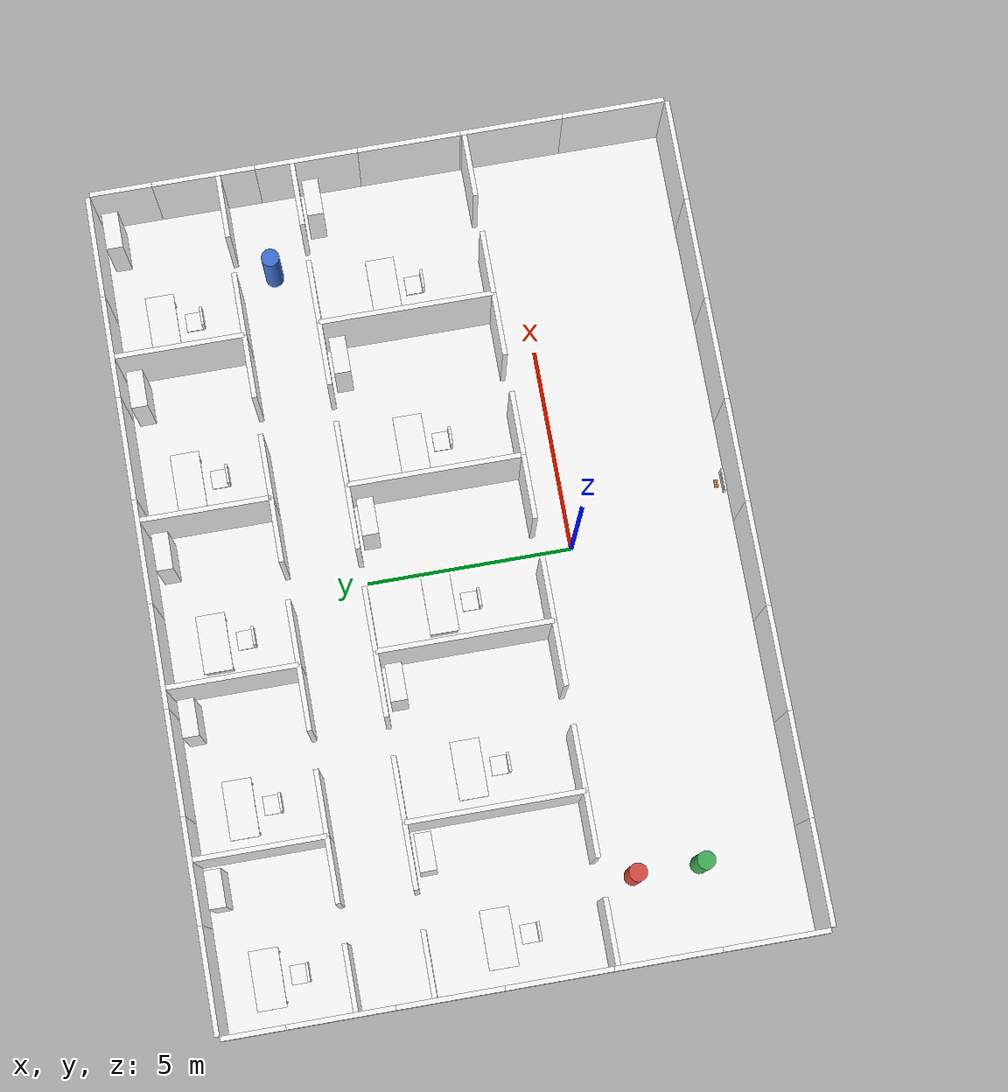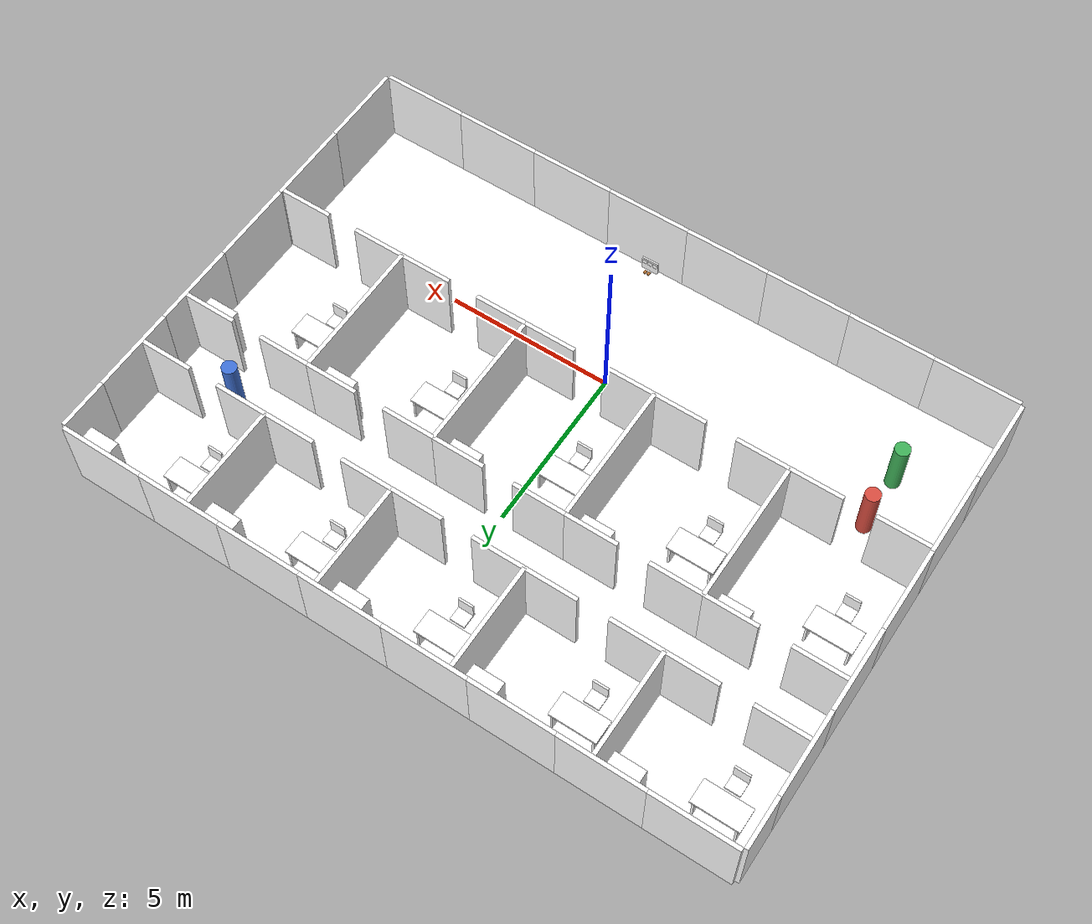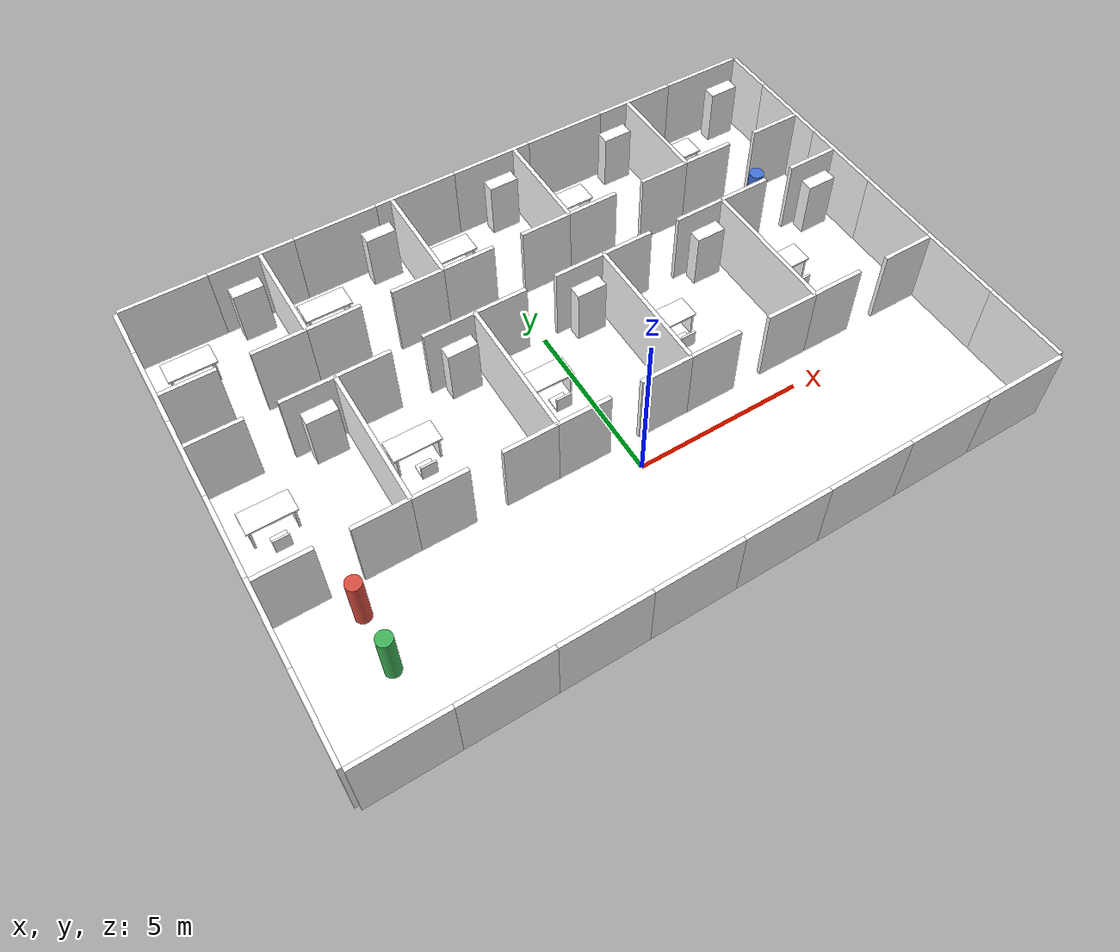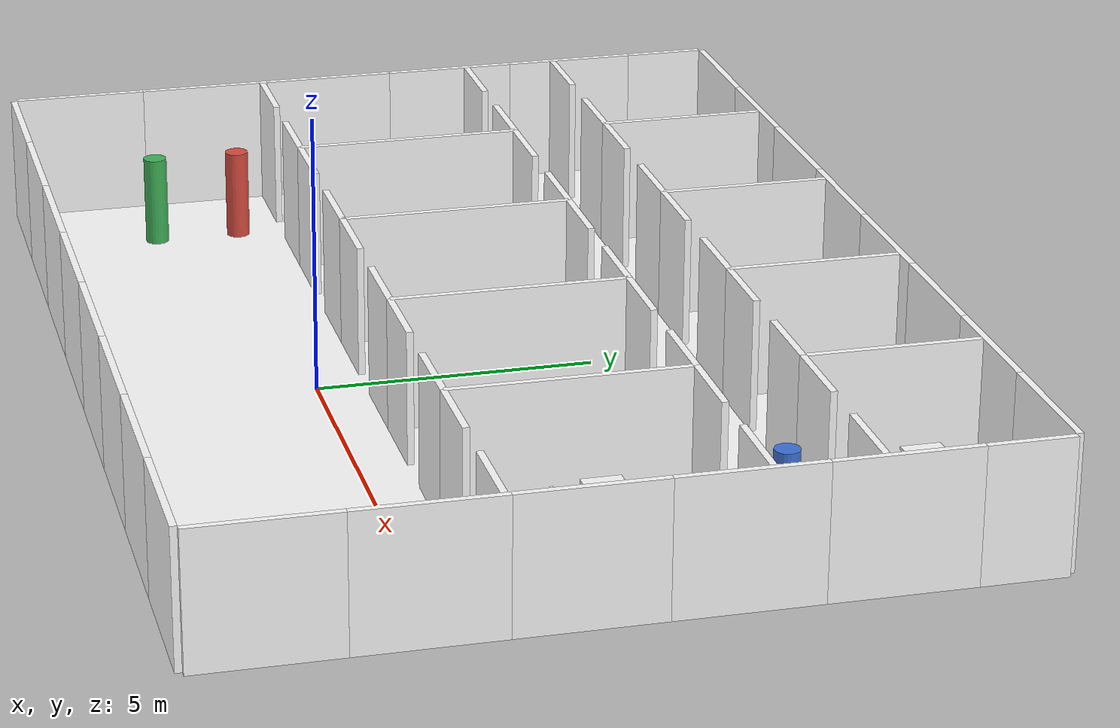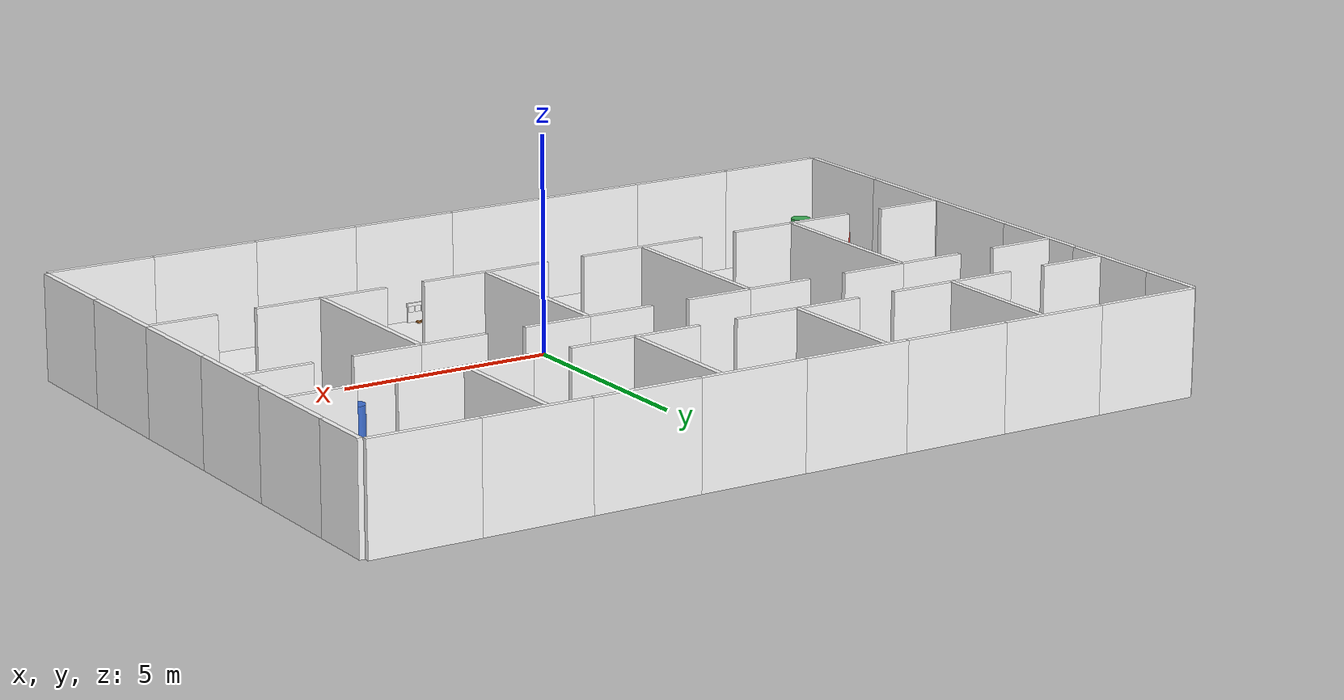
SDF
<?xml version="1.0" ?>
<!-- generate_office.py 로 생성됨. 생성기를 고치세요. -->
<sdf version="1.9">
  <world name="office">

    <physics name="1ms" type="ignored">
      <max_step_size>0.001</max_step_size>
      <real_time_factor>1.0</real_time_factor>
    </physics>
    <plugin filename="gz-sim-physics-system" name="gz::sim::systems::Physics"/>
    <plugin filename="gz-sim-user-commands-system" name="gz::sim::systems::UserCommands"/>
    <plugin filename="gz-sim-scene-broadcaster-system" name="gz::sim::systems::SceneBroadcaster"/>
    <plugin filename="gz-sim-sensors-system" name="gz::sim::systems::Sensors">
      <render_engine>ogre2</render_engine>
    </plugin>
    <plugin filename="gz-sim-imu-system" name="gz::sim::systems::Imu"/>
    <plugin filename="gz-sim-contact-system" name="gz::sim::systems::Contact"/>
    <gravity>0 0 -9.8</gravity>
    <scene>
      <ambient>0.7 0.7 0.7 1</ambient>
      <background>0.8 0.85 0.9 1</background>
      <shadows>true</shadows>
    </scene>
    <!-- 사무실 조명: 그림자를 약하게 둡니다. 밋밋한 벽에 강한 그림자가
         지면 그 경계가 유일한 특징점이 되어, 조명이 바뀌면 지도가 흔들립니다. -->
    <light type="directional" name="ceil1">
      <cast_shadows>true</cast_shadows><pose>0 0 6 0 0 0</pose>
      <diffuse>0.55 0.55 0.55 1</diffuse><specular>0.05 0.05 0.05 1</specular>
      <direction>-0.3 0.2 -0.93</direction>
    </light>
    <light type="directional" name="ceil2">
      <cast_shadows>false</cast_shadows><pose>0 0 6 0 0 0</pose>
      <diffuse>0.4 0.4 0.42 1</diffuse><specular>0 0 0 1</specular>
      <direction>0.4 -0.3 -0.87</direction>
    </light>
    <model name="ground_plane">
      <static>true</static>
      <link name="link">
        <collision name="collision">
          <geometry><plane><normal>0 0 1</normal><size>100 100</size></plane></geometry>
          <surface><friction><ode><mu>1.0</mu><mu2>1.0</mu2></ode></friction></surface>
        </collision>
      </link>
    </model>

    <model name="floor">
      <static>true</static>
      <pose>0.00 3.00 -0.005 0 0 0</pose>
      <link name="link"><visual name="v">
        <geometry><box><size>20.0 14.0 0.01</size></box></geometry>
        <material><diffuse>1 1 1 1</diffuse><pbr><metal>
          <albedo_map>model://room_materials/materials/textures/floor.png</albedo_map><roughness>0.95</roughness>
        </metal></pbr></material>
      </visual></link>
    </model>
    <model name="w_s0">
      <static>true</static>
      <pose>-8.7500 -4.0600 1.2000 0 0 0</pose>
      <link name="link">
      <collision name="c">
        <pose>0 0 0 0 0 0</pose>
        <geometry><box><size>2.5000 0.1200 2.4000</size></box></geometry>
      </collision>
      <visual name="v">
        <pose>0 0 0 0 0 0</pose>
        <geometry><box><size>2.5000 0.1200 2.4000</size></box></geometry>
        <material><diffuse>1 1 1 1</diffuse><pbr><metal>
          <albedo_map>model://room_materials/materials/textures/office_000.png</albedo_map><roughness>0.92</roughness>
        </metal></pbr></material>
      </visual>
      </link>
    </model>
    <model name="w_n1">
      <static>true</static>
      <pose>-8.7500 10.0600 1.2000 0 0 0</pose>
      <link name="link">
      <collision name="c">
        <pose>0 0 0 0 0 0</pose>
        <geometry><box><size>2.5000 0.1200 2.4000</size></box></geometry>
      </collision>
      <visual name="v">
        <pose>0 0 0 0 0 0</pose>
        <geometry><box><size>2.5000 0.1200 2.4000</size></box></geometry>
        <material><diffuse>1 1 1 1</diffuse><pbr><metal>
          <albedo_map>model://room_materials/materials/textures/office_001.png</albedo_map><roughness>0.92</roughness>
        </metal></pbr></material>
      </visual>
      </link>
    </model>
    <model name="w_s2">
      <static>true</static>
      <pose>-6.2500 -4.0600 1.2000 0 0 0</pose>
      <link name="link">
      <collision name="c">
        <pose>0 0 0 0 0 0</pose>
        <geometry><box><size>2.5000 0.1200 2.4000</size></box></geometry>
      </collision>
      <visual name="v">
        <pose>0 0 0 0 0 0</pose>
        <geometry><box><size>2.5000 0.1200 2.4000</size></box></geometry>
        <material><diffuse>1 1 1 1</diffuse><pbr><metal>
          <albedo_map>model://room_materials/materials/textures/office_002.png</albedo_map><roughness>0.92</roughness>
        </metal></pbr></material>
      </visual>
      </link>
    </model>
    <model name="w_n3">
      <static>true</static>
      <pose>-6.2500 10.0600 1.2000 0 0 0</pose>
      <link name="link">
      <collision name="c">
        <pose>0 0 0 0 0 0</pose>
        <geometry><box><size>2.5000 0.1200 2.4000</size></box></geometry>
      </collision>
      <visual name="v">
        <pose>0 0 0 0 0 0</pose>
        <geometry><box><size>2.5000 0.1200 2.4000</size></box></geometry>
        <material><diffuse>1 1 1 1</diffuse><pbr><metal>
          <albedo_map>model://room_materials/materials/textures/office_003.png</albedo_map><roughness>0.92</roughness>
        </metal></pbr></material>
      </visual>
      </link>
    </model>
    <model name="w_s4">
      <static>true</static>
      <pose>-3.7500 -4.0600 1.2000 0 0 0</pose>
      <link name="link">
      <collision name="c">
        <pose>0 0 0 0 0 0</pose>
        <geometry><box><size>2.5000 0.1200 2.4000</size></box></geometry>
      </collision>
      <visual name="v">
        <pose>0 0 0 0 0 0</pose>
        <geometry><box><size>2.5000 0.1200 2.4000</size></box></geometry>
        <material><diffuse>1 1 1 1</diffuse><pbr><metal>
          <albedo_map>model://room_materials/materials/textures/office_004.png</albedo_map><roughness>0.92</roughness>
        </metal></pbr></material>
      </visual>
      </link>
    </model>
    <model name="w_n5">
      <static>true</static>
      <pose>-3.7500 10.0600 1.2000 0 0 0</pose>
      <link name="link">
      <collision name="c">
        <pose>0 0 0 0 0 0</pose>
        <geometry><box><size>2.5000 0.1200 2.4000</size></box></geometry>
      </collision>
      <visual name="v">
        <pose>0 0 0 0 0 0</pose>
        <geometry><box><size>2.5000 0.1200 2.4000</size></box></geometry>
        <material><diffuse>1 1 1 1</diffuse><pbr><metal>
          <albedo_map>model://room_materials/materials/textures/office_005.png</albedo_map><roughness>0.92</roughness>
        </metal></pbr></material>
      </visual>
      </link>
    </model>
    <model name="w_s6">
      <static>true</static>
      <pose>-1.2500 -4.0600 1.2000 0 0 0</pose>
      <link name="link">
      <collision name="c">
        <pose>0 0 0 0 0 0</pose>
        <geometry><box><size>2.5000 0.1200 2.4000</size></box></geometry>
      </collision>
      <visual name="v">
        <pose>0 0 0 0 0 0</pose>
        <geometry><box><size>2.5000 0.1200 2.4000</size></box></geometry>
        <material><diffuse>1 1 1 1</diffuse><pbr><metal>
          <albedo_map>model://room_materials/materials/textures/office_006.png</albedo_map><roughness>0.92</roughness>
        </metal></pbr></material>
      </visual>
      </link>
    </model>
    <model name="w_n7">
      <static>true</static>
      <pose>-1.2500 10.0600 1.2000 0 0 0</pose>
      <link name="link">
      <collision name="c">
        <pose>0 0 0 0 0 0</pose>
        <geometry><box><size>2.5000 0.1200 2.4000</size></box></geometry>
      </collision>
      <visual name="v">
        <pose>0 0 0 0 0 0</pose>
        <geometry><box><size>2.5000 0.1200 2.4000</size></box></geometry>
        <material><diffuse>1 1 1 1</diffuse><pbr><metal>
          <albedo_map>model://room_materials/materials/textures/office_007.png</albedo_map><roughness>0.92</roughness>
        </metal></pbr></material>
      </visual>
      </link>
    </model>
    <model name="w_s8">
      <static>true</static>
      <pose>1.2500 -4.0600 1.2000 0 0 0</pose>
      <link name="link">
      <collision name="c">
        <pose>0 0 0 0 0 0</pose>
        <geometry><box><size>2.5000 0.1200 2.4000</size></box></geometry>
      </collision>
      <visual name="v">
        <pose>0 0 0 0 0 0</pose>
        <geometry><box><size>2.5000 0.1200 2.4000</size></box></geometry>
        <material><diffuse>1 1 1 1</diffuse><pbr><metal>
          <albedo_map>model://room_materials/materials/textures/office_008.png</albedo_map><roughness>0.92</roughness>
        </metal></pbr></material>
      </visual>
      </link>
    </model>
    <model name="w_n9">
      <static>true</static>
      <pose>1.2500 10.0600 1.2000 0 0 0</pose>
      <link name="link">
      <collision name="c">
        <pose>0 0 0 0 0 0</pose>
        <geometry><box><size>2.5000 0.1200 2.4000</size></box></geometry>
      </collision>
      <visual name="v">
        <pose>0 0 0 0 0 0</pose>
        <geometry><box><size>2.5000 0.1200 2.4000</size></box></geometry>
        <material><diffuse>1 1 1 1</diffuse><pbr><metal>
          <albedo_map>model://room_materials/materials/textures/office_009.png</albedo_map><roughness>0.92</roughness>
        </metal></pbr></material>
      </visual>
      </link>
    </model>
    <model name="w_s10">
      <static>true</static>
      <pose>3.7500 -4.0600 1.2000 0 0 0</pose>
      <link name="link">
      <collision name="c">
        <pose>0 0 0 0 0 0</pose>
        <geometry><box><size>2.5000 0.1200 2.4000</size></box></geometry>
      </collision>
      <visual name="v">
        <pose>0 0 0 0 0 0</pose>
        <geometry><box><size>2.5000 0.1200 2.4000</size></box></geometry>
        <material><diffuse>1 1 1 1</diffuse><pbr><metal>
          <albedo_map>model://room_materials/materials/textures/office_010.png</albedo_map><roughness>0.92</roughness>
        </metal></pbr></material>
      </visual>
      </link>
    </model>
    <model name="w_n11">
      <static>true</static>
      <pose>3.7500 10.0600 1.2000 0 0 0</pose>
      <link name="link">
      <collision name="c">
        <pose>0 0 0 0 0 0</pose>
        <geometry><box><size>2.5000 0.1200 2.4000</size></box></geometry>
      </collision>
      <visual name="v">
        <pose>0 0 0 0 0 0</pose>
        <geometry><box><size>2.5000 0.1200 2.4000</size></box></geometry>
        <material><diffuse>1 1 1 1</diffuse><pbr><metal>
          <albedo_map>model://room_materials/materials/textures/office_011.png</albedo_map><roughness>0.92</roughness>
        </metal></pbr></material>
      </visual>
      </link>
    </model>
    <model name="w_s12">
      <static>true</static>
      <pose>6.2500 -4.0600 1.2000 0 0 0</pose>
      <link name="link">
      <collision name="c">
        <pose>0 0 0 0 0 0</pose>
        <geometry><box><size>2.5000 0.1200 2.4000</size></box></geometry>
      </collision>
      <visual name="v">
        <pose>0 0 0 0 0 0</pose>
        <geometry><box><size>2.5000 0.1200 2.4000</size></box></geometry>
        <material><diffuse>1 1 1 1</diffuse><pbr><metal>
          <albedo_map>model://room_materials/materials/textures/office_012.png</albedo_map><roughness>0.92</roughness>
        </metal></pbr></material>
      </visual>
      </link>
    </model>
    <model name="w_n13">
      <static>true</static>
      <pose>6.2500 10.0600 1.2000 0 0 0</pose>
      <link name="link">
      <collision name="c">
        <pose>0 0 0 0 0 0</pose>
        <geometry><box><size>2.5000 0.1200 2.4000</size></box></geometry>
      </collision>
      <visual name="v">
        <pose>0 0 0 0 0 0</pose>
        <geometry><box><size>2.5000 0.1200 2.4000</size></box></geometry>
        <material><diffuse>1 1 1 1</diffuse><pbr><metal>
          <albedo_map>model://room_materials/materials/textures/office_013.png</albedo_map><roughness>0.92</roughness>
        </metal></pbr></material>
      </visual>
      </link>
    </model>
    <model name="w_s14">
      <static>true</static>
      <pose>8.7500 -4.0600 1.2000 0 0 0</pose>
      <link name="link">
      <collision name="c">
        <pose>0 0 0 0 0 0</pose>
        <geometry><box><size>2.5000 0.1200 2.4000</size></box></geometry>
      </collision>
      <visual name="v">
        <pose>0 0 0 0 0 0</pose>
        <geometry><box><size>2.5000 0.1200 2.4000</size></box></geometry>
        <material><diffuse>1 1 1 1</diffuse><pbr><metal>
          <albedo_map>model://room_materials/materials/textures/office_014.png</albedo_map><roughness>0.92</roughness>
        </metal></pbr></material>
      </visual>
      </link>
    </model>
    <model name="w_n15">
      <static>true</static>
      <pose>8.7500 10.0600 1.2000 0 0 0</pose>
      <link name="link">
      <collision name="c">
        <pose>0 0 0 0 0 0</pose>
        <geometry><box><size>2.5000 0.1200 2.4000</size></box></geometry>
      </collision>
      <visual name="v">
        <pose>0 0 0 0 0 0</pose>
        <geometry><box><size>2.5000 0.1200 2.4000</size></box></geometry>
        <material><diffuse>1 1 1 1</diffuse><pbr><metal>
          <albedo_map>model://room_materials/materials/textures/office_015.png</albedo_map><roughness>0.92</roughness>
        </metal></pbr></material>
      </visual>
      </link>
    </model>
    <model name="w_w16">
      <static>true</static>
      <pose>-10.0600 -2.7500 1.2000 0 0 0</pose>
      <link name="link">
      <collision name="c">
        <pose>0 0 0 0 0 0</pose>
        <geometry><box><size>0.1200 2.5000 2.4000</size></box></geometry>
      </collision>
      <visual name="v">
        <pose>0 0 0 0 0 0</pose>
        <geometry><box><size>0.1200 2.5000 2.4000</size></box></geometry>
        <material><diffuse>1 1 1 1</diffuse><pbr><metal>
          <albedo_map>model://room_materials/materials/textures/office_016.png</albedo_map><roughness>0.92</roughness>
        </metal></pbr></material>
      </visual>
      </link>
    </model>
    <model name="w_e17">
      <static>true</static>
      <pose>10.0600 -2.7500 1.2000 0 0 0</pose>
      <link name="link">
      <collision name="c">
        <pose>0 0 0 0 0 0</pose>
        <geometry><box><size>0.1200 2.5000 2.4000</size></box></geometry>
      </collision>
      <visual name="v">
        <pose>0 0 0 0 0 0</pose>
        <geometry><box><size>0.1200 2.5000 2.4000</size></box></geometry>
        <material><diffuse>1 1 1 1</diffuse><pbr><metal>
          <albedo_map>model://room_materials/materials/textures/office_017.png</albedo_map><roughness>0.92</roughness>
        </metal></pbr></material>
      </visual>
      </link>
    </model>
    <model name="w_w18">
      <static>true</static>
      <pose>-10.0600 -0.2500 1.2000 0 0 0</pose>
      <link name="link">
      <collision name="c">
        <pose>0 0 0 0 0 0</pose>
        <geometry><box><size>0.1200 2.5000 2.4000</size></box></geometry>
      </collision>
      <visual name="v">
        <pose>0 0 0 0 0 0</pose>
        <geometry><box><size>0.1200 2.5000 2.4000</size></box></geometry>
        <material><diffuse>1 1 1 1</diffuse><pbr><metal>
          <albedo_map>model://room_materials/materials/textures/office_018.png</albedo_map><roughness>0.92</roughness>
        </metal></pbr></material>
      </visual>
      </link>
    </model>
    <model name="w_e19">
      <static>true</static>
      <pose>10.0600 -0.2500 1.2000 0 0 0</pose>
      <link name="link">
      <collision name="c">
        <pose>0 0 0 0 0 0</pose>
        <geometry><box><size>0.1200 2.5000 2.4000</size></box></geometry>
      </collision>
      <visual name="v">
        <pose>0 0 0 0 0 0</pose>
        <geometry><box><size>0.1200 2.5000 2.4000</size></box></geometry>
        <material><diffuse>1 1 1 1</diffuse><pbr><metal>
          <albedo_map>model://room_materials/materials/textures/office_019.png</albedo_map><roughness>0.92</roughness>
        </metal></pbr></material>
      </visual>
      </link>
    </model>
    <model name="w_w20">
      <static>true</static>
      <pose>-10.0600 2.2500 1.2000 0 0 0</pose>
      <link name="link">
      <collision name="c">
        <pose>0 0 0 0 0 0</pose>
        <geometry><box><size>0.1200 2.5000 2.4000</size></box></geometry>
      </collision>
      <visual name="v">
        <pose>0 0 0 0 0 0</pose>
        <geometry><box><size>0.1200 2.5000 2.4000</size></box></geometry>
        <material><diffuse>1 1 1 1</diffuse><pbr><metal>
          <albedo_map>model://room_materials/materials/textures/office_020.png</albedo_map><roughness>0.92</roughness>
        </metal></pbr></material>
      </visual>
      </link>
    </model>
    <model name="w_e21">
      <static>true</static>
      <pose>10.0600 2.2500 1.2000 0 0 0</pose>
      <link name="link">
      <collision name="c">
        <pose>0 0 0 0 0 0</pose>
        <geometry><box><size>0.1200 2.5000 2.4000</size></box></geometry>
      </collision>
      <visual name="v">
        <pose>0 0 0 0 0 0</pose>
        <geometry><box><size>0.1200 2.5000 2.4000</size></box></geometry>
        <material><diffuse>1 1 1 1</diffuse><pbr><metal>
          <albedo_map>model://room_materials/materials/textures/office_021.png</albedo_map><roughness>0.92</roughness>
        </metal></pbr></material>
      </visual>
      </link>
    </model>
    <model name="w_w22">
      <static>true</static>
      <pose>-10.0600 4.7500 1.2000 0 0 0</pose>
      <link name="link">
      <collision name="c">
        <pose>0 0 0 0 0 0</pose>
        <geometry><box><size>0.1200 2.5000 2.4000</size></box></geometry>
      </collision>
      <visual name="v">
        <pose>0 0 0 0 0 0</pose>
        <geometry><box><size>0.1200 2.5000 2.4000</size></box></geometry>
        <material><diffuse>1 1 1 1</diffuse><pbr><metal>
          <albedo_map>model://room_materials/materials/textures/office_022.png</albedo_map><roughness>0.92</roughness>
        </metal></pbr></material>
      </visual>
      </link>
    </model>
    <model name="w_e23">
      <static>true</static>
      <pose>10.0600 4.7500 1.2000 0 0 0</pose>
      <link name="link">
      <collision name="c">
        <pose>0 0 0 0 0 0</pose>
        <geometry><box><size>0.1200 2.5000 2.4000</size></box></geometry>
      </collision>
      <visual name="v">
        <pose>0 0 0 0 0 0</pose>
        <geometry><box><size>0.1200 2.5000 2.4000</size></box></geometry>
        <material><diffuse>1 1 1 1</diffuse><pbr><metal>
          <albedo_map>model://room_materials/materials/textures/office_023.png</albedo_map><roughness>0.92</roughness>
        </metal></pbr></material>
      </visual>
      </link>
    </model>
    <model name="w_w24">
      <static>true</static>
      <pose>-10.0600 7.2500 1.2000 0 0 0</pose>
      <link name="link">
      <collision name="c">
        <pose>0 0 0 0 0 0</pose>
        <geometry><box><size>0.1200 2.5000 2.4000</size></box></geometry>
      </collision>
      <visual name="v">
        <pose>0 0 0 0 0 0</pose>
        <geometry><box><size>0.1200 2.5000 2.4000</size></box></geometry>
        <material><diffuse>1 1 1 1</diffuse><pbr><metal>
          <albedo_map>model://room_materials/materials/textures/office_024.png</albedo_map><roughness>0.92</roughness>
        </metal></pbr></material>
      </visual>
      </link>
    </model>
    <model name="w_e25">
      <static>true</static>
      <pose>10.0600 7.2500 1.2000 0 0 0</pose>
      <link name="link">
      <collision name="c">
        <pose>0 0 0 0 0 0</pose>
        <geometry><box><size>0.1200 2.5000 2.4000</size></box></geometry>
      </collision>
      <visual name="v">
        <pose>0 0 0 0 0 0</pose>
        <geometry><box><size>0.1200 2.5000 2.4000</size></box></geometry>
        <material><diffuse>1 1 1 1</diffuse><pbr><metal>
          <albedo_map>model://room_materials/materials/textures/office_025.png</albedo_map><roughness>0.92</roughness>
        </metal></pbr></material>
      </visual>
      </link>
    </model>
    <model name="w_w26">
      <static>true</static>
      <pose>-10.0600 9.2500 1.2000 0 0 0</pose>
      <link name="link">
      <collision name="c">
        <pose>0 0 0 0 0 0</pose>
        <geometry><box><size>0.1200 1.5000 2.4000</size></box></geometry>
      </collision>
      <visual name="v">
        <pose>0 0 0 0 0 0</pose>
        <geometry><box><size>0.1200 1.5000 2.4000</size></box></geometry>
        <material><diffuse>1 1 1 1</diffuse><pbr><metal>
          <albedo_map>model://room_materials/materials/textures/office_026.png</albedo_map><roughness>0.92</roughness>
        </metal></pbr></material>
      </visual>
      </link>
    </model>
    <model name="w_e27">
      <static>true</static>
      <pose>10.0600 9.2500 1.2000 0 0 0</pose>
      <link name="link">
      <collision name="c">
        <pose>0 0 0 0 0 0</pose>
        <geometry><box><size>0.1200 1.5000 2.4000</size></box></geometry>
      </collision>
      <visual name="v">
        <pose>0 0 0 0 0 0</pose>
        <geometry><box><size>0.1200 1.5000 2.4000</size></box></geometry>
        <material><diffuse>1 1 1 1</diffuse><pbr><metal>
          <albedo_map>model://room_materials/materials/textures/office_027.png</albedo_map><roughness>0.92</roughness>
        </metal></pbr></material>
      </visual>
      </link>
    </model>
    <model name="cA_n_0a">
      <static>true</static>
      <pose>-9.2250 0.9000 1.2000 0 0 0</pose>
      <link name="link">
      <collision name="c">
        <pose>0 0 0 0 0 0</pose>
        <geometry><box><size>1.5500 0.1200 2.4000</size></box></geometry>
      </collision>
      <visual name="v">
        <pose>0 0 0 0 0 0</pose>
        <geometry><box><size>1.5500 0.1200 2.4000</size></box></geometry>
        <material><diffuse>1 1 1 1</diffuse><pbr><metal>
          <albedo_map>model://room_materials/materials/textures/office_028.png</albedo_map><roughness>0.92</roughness>
        </metal></pbr></material>
      </visual>
      </link>
    </model>
    <model name="cA_n_0b">
      <static>true</static>
      <pose>-6.7750 0.9000 1.2000 0 0 0</pose>
      <link name="link">
      <collision name="c">
        <pose>0 0 0 0 0 0</pose>
        <geometry><box><size>1.5500 0.1200 2.4000</size></box></geometry>
      </collision>
      <visual name="v">
        <pose>0 0 0 0 0 0</pose>
        <geometry><box><size>1.5500 0.1200 2.4000</size></box></geometry>
        <material><diffuse>1 1 1 1</diffuse><pbr><metal>
          <albedo_map>model://room_materials/materials/textures/office_029.png</albedo_map><roughness>0.92</roughness>
        </metal></pbr></material>
      </visual>
      </link>
    </model>
    <model name="cA_n_1a">
      <static>true</static>
      <pose>-5.2250 0.9000 1.2000 0 0 0</pose>
      <link name="link">
      <collision name="c">
        <pose>0 0 0 0 0 0</pose>
        <geometry><box><size>1.5500 0.1200 2.4000</size></box></geometry>
      </collision>
      <visual name="v">
        <pose>0 0 0 0 0 0</pose>
        <geometry><box><size>1.5500 0.1200 2.4000</size></box></geometry>
        <material><diffuse>1 1 1 1</diffuse><pbr><metal>
          <albedo_map>model://room_materials/materials/textures/office_030.png</albedo_map><roughness>0.92</roughness>
        </metal></pbr></material>
      </visual>
      </link>
    </model>
    <model name="cA_n_1b">
      <static>true</static>
      <pose>-2.7750 0.9000 1.2000 0 0 0</pose>
      <link name="link">
      <collision name="c">
        <pose>0 0 0 0 0 0</pose>
        <geometry><box><size>1.5500 0.1200 2.4000</size></box></geometry>
      </collision>
      <visual name="v">
        <pose>0 0 0 0 0 0</pose>
        <geometry><box><size>1.5500 0.1200 2.4000</size></box></geometry>
        <material><diffuse>1 1 1 1</diffuse><pbr><metal>
          <albedo_map>model://room_materials/materials/textures/office_031.png</albedo_map><roughness>0.92</roughness>
        </metal></pbr></material>
      </visual>
      </link>
    </model>
    <model name="cA_n_2a">
      <static>true</static>
      <pose>-1.2250 0.9000 1.2000 0 0 0</pose>
      <link name="link">
      <collision name="c">
        <pose>0 0 0 0 0 0</pose>
        <geometry><box><size>1.5500 0.1200 2.4000</size></box></geometry>
      </collision>
      <visual name="v">
        <pose>0 0 0 0 0 0</pose>
        <geometry><box><size>1.5500 0.1200 2.4000</size></box></geometry>
        <material><diffuse>1 1 1 1</diffuse><pbr><metal>
          <albedo_map>model://room_materials/materials/textures/office_032.png</albedo_map><roughness>0.92</roughness>
        </metal></pbr></material>
      </visual>
      </link>
    </model>
    <model name="cA_n_2b">
      <static>true</static>
      <pose>1.2250 0.9000 1.2000 0 0 0</pose>
      <link name="link">
      <collision name="c">
        <pose>0 0 0 0 0 0</pose>
        <geometry><box><size>1.5500 0.1200 2.4000</size></box></geometry>
      </collision>
      <visual name="v">
        <pose>0 0 0 0 0 0</pose>
        <geometry><box><size>1.5500 0.1200 2.4000</size></box></geometry>
        <material><diffuse>1 1 1 1</diffuse><pbr><metal>
          <albedo_map>model://room_materials/materials/textures/office_033.png</albedo_map><roughness>0.92</roughness>
        </metal></pbr></material>
      </visual>
      </link>
    </model>
    <model name="cA_n_3a">
      <static>true</static>
      <pose>2.7750 0.9000 1.2000 0 0 0</pose>
      <link name="link">
      <collision name="c">
        <pose>0 0 0 0 0 0</pose>
        <geometry><box><size>1.5500 0.1200 2.4000</size></box></geometry>
      </collision>
      <visual name="v">
        <pose>0 0 0 0 0 0</pose>
        <geometry><box><size>1.5500 0.1200 2.4000</size></box></geometry>
        <material><diffuse>1 1 1 1</diffuse><pbr><metal>
          <albedo_map>model://room_materials/materials/textures/office_034.png</albedo_map><roughness>0.92</roughness>
        </metal></pbr></material>
      </visual>
      </link>
    </model>
    <model name="cA_n_3b">
      <static>true</static>
      <pose>5.2250 0.9000 1.2000 0 0 0</pose>
      <link name="link">
      <collision name="c">
        <pose>0 0 0 0 0 0</pose>
        <geometry><box><size>1.5500 0.1200 2.4000</size></box></geometry>
      </collision>
      <visual name="v">
        <pose>0 0 0 0 0 0</pose>
        <geometry><box><size>1.5500 0.1200 2.4000</size></box></geometry>
        <material><diffuse>1 1 1 1</diffuse><pbr><metal>
          <albedo_map>model://room_materials/materials/textures/office_035.png</albedo_map><roughness>0.92</roughness>
        </metal></pbr></material>
      </visual>
      </link>
    </model>
    <model name="cA_n_4a">
      <static>true</static>
      <pose>6.7750 0.9000 1.2000 0 0 0</pose>
      <link name="link">
      <collision name="c">
        <pose>0 0 0 0 0 0</pose>
        <geometry><box><size>1.5500 0.1200 2.4000</size></box></geometry>
      </collision>
      <visual name="v">
        <pose>0 0 0 0 0 0</pose>
        <geometry><box><size>1.5500 0.1200 2.4000</size></box></geometry>
        <material><diffuse>1 1 1 1</diffuse><pbr><metal>
          <albedo_map>model://room_materials/materials/textures/office_036.png</albedo_map><roughness>0.92</roughness>
        </metal></pbr></material>
      </visual>
      </link>
    </model>
    <model name="cA_n_4b">
      <static>true</static>
      <pose>9.2250 0.9000 1.2000 0 0 0</pose>
      <link name="link">
      <collision name="c">
        <pose>0 0 0 0 0 0</pose>
        <geometry><box><size>1.5500 0.1200 2.4000</size></box></geometry>
      </collision>
      <visual name="v">
        <pose>0 0 0 0 0 0</pose>
        <geometry><box><size>1.5500 0.1200 2.4000</size></box></geometry>
        <material><diffuse>1 1 1 1</diffuse><pbr><metal>
          <albedo_map>model://room_materials/materials/textures/office_037.png</albedo_map><roughness>0.92</roughness>
        </metal></pbr></material>
      </visual>
      </link>
    </model>
    <model name="cB_s_0a">
      <static>true</static>
      <pose>-9.2250 5.1000 1.2000 0 0 0</pose>
      <link name="link">
      <collision name="c">
        <pose>0 0 0 0 0 0</pose>
        <geometry><box><size>1.5500 0.1200 2.4000</size></box></geometry>
      </collision>
      <visual name="v">
        <pose>0 0 0 0 0 0</pose>
        <geometry><box><size>1.5500 0.1200 2.4000</size></box></geometry>
        <material><diffuse>1 1 1 1</diffuse><pbr><metal>
          <albedo_map>model://room_materials/materials/textures/office_038.png</albedo_map><roughness>0.92</roughness>
        </metal></pbr></material>
      </visual>
      </link>
    </model>
    <model name="cB_s_0b">
      <static>true</static>
      <pose>-6.7750 5.1000 1.2000 0 0 0</pose>
      <link name="link">
      <collision name="c">
        <pose>0 0 0 0 0 0</pose>
        <geometry><box><size>1.5500 0.1200 2.4000</size></box></geometry>
      </collision>
      <visual name="v">
        <pose>0 0 0 0 0 0</pose>
        <geometry><box><size>1.5500 0.1200 2.4000</size></box></geometry>
        <material><diffuse>1 1 1 1</diffuse><pbr><metal>
          <albedo_map>model://room_materials/materials/textures/office_039.png</albedo_map><roughness>0.92</roughness>
        </metal></pbr></material>
      </visual>
      </link>
    </model>
    <model name="cB_s_1a">
      <static>true</static>
      <pose>-5.2250 5.1000 1.2000 0 0 0</pose>
      <link name="link">
      <collision name="c">
        <pose>0 0 0 0 0 0</pose>
        <geometry><box><size>1.5500 0.1200 2.4000</size></box></geometry>
      </collision>
      <visual name="v">
        <pose>0 0 0 0 0 0</pose>
        <geometry><box><size>1.5500 0.1200 2.4000</size></box></geometry>
        <material><diffuse>1 1 1 1</diffuse><pbr><metal>
          <albedo_map>model://room_materials/materials/textures/office_040.png</albedo_map><roughness>0.92</roughness>
        </metal></pbr></material>
      </visual>
      </link>
    </model>
    <model name="cB_s_1b">
      <static>true</static>
      <pose>-2.7750 5.1000 1.2000 0 0 0</pose>
      <link name="link">
      <collision name="c">
        <pose>0 0 0 0 0 0</pose>
        <geometry><box><size>1.5500 0.1200 2.4000</size></box></geometry>
      </collision>
      <visual name="v">
        <pose>0 0 0 0 0 0</pose>
        <geometry><box><size>1.5500 0.1200 2.4000</size></box></geometry>
        <material><diffuse>1 1 1 1</diffuse><pbr><metal>
          <albedo_map>model://room_materials/materials/textures/office_041.png</albedo_map><roughness>0.92</roughness>
        </metal></pbr></material>
      </visual>
      </link>
    </model>
    <model name="cB_s_2a">
      <static>true</static>
      <pose>-1.2250 5.1000 1.2000 0 0 0</pose>
      <link name="link">
      <collision name="c">
        <pose>0 0 0 0 0 0</pose>
        <geometry><box><size>1.5500 0.1200 2.4000</size></box></geometry>
      </collision>
      <visual name="v">
        <pose>0 0 0 0 0 0</pose>
        <geometry><box><size>1.5500 0.1200 2.4000</size></box></geometry>
        <material><diffuse>1 1 1 1</diffuse><pbr><metal>
          <albedo_map>model://room_materials/materials/textures/office_042.png</albedo_map><roughness>0.92</roughness>
        </metal></pbr></material>
      </visual>
      </link>
    </model>
    <model name="cB_s_2b">
      <static>true</static>
      <pose>1.2250 5.1000 1.2000 0 0 0</pose>
      <link name="link">
      <collision name="c">
        <pose>0 0 0 0 0 0</pose>
        <geometry><box><size>1.5500 0.1200 2.4000</size></box></geometry>
      </collision>
      <visual name="v">
        <pose>0 0 0 0 0 0</pose>
        <geometry><box><size>1.5500 0.1200 2.4000</size></box></geometry>
        <material><diffuse>1 1 1 1</diffuse><pbr><metal>
          <albedo_map>model://room_materials/materials/textures/office_043.png</albedo_map><roughness>0.92</roughness>
        </metal></pbr></material>
      </visual>
      </link>
    </model>
    <model name="cB_s_3a">
      <static>true</static>
      <pose>2.7750 5.1000 1.2000 0 0 0</pose>
      <link name="link">
      <collision name="c">
        <pose>0 0 0 0 0 0</pose>
        <geometry><box><size>1.5500 0.1200 2.4000</size></box></geometry>
      </collision>
      <visual name="v">
        <pose>0 0 0 0 0 0</pose>
        <geometry><box><size>1.5500 0.1200 2.4000</size></box></geometry>
        <material><diffuse>1 1 1 1</diffuse><pbr><metal>
          <albedo_map>model://room_materials/materials/textures/office_044.png</albedo_map><roughness>0.92</roughness>
        </metal></pbr></material>
      </visual>
      </link>
    </model>
    <model name="cB_s_3b">
      <static>true</static>
      <pose>5.2250 5.1000 1.2000 0 0 0</pose>
      <link name="link">
      <collision name="c">
        <pose>0 0 0 0 0 0</pose>
        <geometry><box><size>1.5500 0.1200 2.4000</size></box></geometry>
      </collision>
      <visual name="v">
        <pose>0 0 0 0 0 0</pose>
        <geometry><box><size>1.5500 0.1200 2.4000</size></box></geometry>
        <material><diffuse>1 1 1 1</diffuse><pbr><metal>
          <albedo_map>model://room_materials/materials/textures/office_045.png</albedo_map><roughness>0.92</roughness>
        </metal></pbr></material>
      </visual>
      </link>
    </model>
    <model name="cB_s_4a">
      <static>true</static>
      <pose>6.7750 5.1000 1.2000 0 0 0</pose>
      <link name="link">
      <collision name="c">
        <pose>0 0 0 0 0 0</pose>
        <geometry><box><size>1.5500 0.1200 2.4000</size></box></geometry>
      </collision>
      <visual name="v">
        <pose>0 0 0 0 0 0</pose>
        <geometry><box><size>1.5500 0.1200 2.4000</size></box></geometry>
        <material><diffuse>1 1 1 1</diffuse><pbr><metal>
          <albedo_map>model://room_materials/materials/textures/office_046.png</albedo_map><roughness>0.92</roughness>
        </metal></pbr></material>
      </visual>
      </link>
    </model>
    <model name="cB_s_4b">
      <static>true</static>
      <pose>9.2250 5.1000 1.2000 0 0 0</pose>
      <link name="link">
      <collision name="c">
        <pose>0 0 0 0 0 0</pose>
        <geometry><box><size>1.5500 0.1200 2.4000</size></box></geometry>
      </collision>
      <visual name="v">
        <pose>0 0 0 0 0 0</pose>
        <geometry><box><size>1.5500 0.1200 2.4000</size></box></geometry>
        <material><diffuse>1 1 1 1</diffuse><pbr><metal>
          <albedo_map>model://room_materials/materials/textures/office_047.png</albedo_map><roughness>0.92</roughness>
        </metal></pbr></material>
      </visual>
      </link>
    </model>
    <model name="cB_n_0a">
      <static>true</static>
      <pose>-9.2250 6.9000 1.2000 0 0 0</pose>
      <link name="link">
      <collision name="c">
        <pose>0 0 0 0 0 0</pose>
        <geometry><box><size>1.5500 0.1200 2.4000</size></box></geometry>
      </collision>
      <visual name="v">
        <pose>0 0 0 0 0 0</pose>
        <geometry><box><size>1.5500 0.1200 2.4000</size></box></geometry>
        <material><diffuse>1 1 1 1</diffuse><pbr><metal>
          <albedo_map>model://room_materials/materials/textures/office_048.png</albedo_map><roughness>0.92</roughness>
        </metal></pbr></material>
      </visual>
      </link>
    </model>
    <model name="cB_n_0b">
      <static>true</static>
      <pose>-6.7750 6.9000 1.2000 0 0 0</pose>
      <link name="link">
      <collision name="c">
        <pose>0 0 0 0 0 0</pose>
        <geometry><box><size>1.5500 0.1200 2.4000</size></box></geometry>
      </collision>
      <visual name="v">
        <pose>0 0 0 0 0 0</pose>
        <geometry><box><size>1.5500 0.1200 2.4000</size></box></geometry>
        <material><diffuse>1 1 1 1</diffuse><pbr><metal>
          <albedo_map>model://room_materials/materials/textures/office_049.png</albedo_map><roughness>0.92</roughness>
        </metal></pbr></material>
      </visual>
      </link>
    </model>
    <model name="cB_n_1a">
      <static>true</static>
      <pose>-5.2250 6.9000 1.2000 0 0 0</pose>
      <link name="link">
      <collision name="c">
        <pose>0 0 0 0 0 0</pose>
        <geometry><box><size>1.5500 0.1200 2.4000</size></box></geometry>
      </collision>
      <visual name="v">
        <pose>0 0 0 0 0 0</pose>
        <geometry><box><size>1.5500 0.1200 2.4000</size></box></geometry>
        <material><diffuse>1 1 1 1</diffuse><pbr><metal>
          <albedo_map>model://room_materials/materials/textures/office_050.png</albedo_map><roughness>0.92</roughness>
        </metal></pbr></material>
      </visual>
      </link>
    </model>
    <model name="cB_n_1b">
      <static>true</static>
      <pose>-2.7750 6.9000 1.2000 0 0 0</pose>
      <link name="link">
      <collision name="c">
        <pose>0 0 0 0 0 0</pose>
        <geometry><box><size>1.5500 0.1200 2.4000</size></box></geometry>
      </collision>
      <visual name="v">
        <pose>0 0 0 0 0 0</pose>
        <geometry><box><size>1.5500 0.1200 2.4000</size></box></geometry>
        <material><diffuse>1 1 1 1</diffuse><pbr><metal>
          <albedo_map>model://room_materials/materials/textures/office_051.png</albedo_map><roughness>0.92</roughness>
        </metal></pbr></material>
      </visual>
      </link>
    </model>
    <model name="cB_n_2a">
      <static>true</static>
      <pose>-1.2250 6.9000 1.2000 0 0 0</pose>
      <link name="link">
      <collision name="c">
        <pose>0 0 0 0 0 0</pose>
        <geometry><box><size>1.5500 0.1200 2.4000</size></box></geometry>
      </collision>
      <visual name="v">
        <pose>0 0 0 0 0 0</pose>
        <geometry><box><size>1.5500 0.1200 2.4000</size></box></geometry>
        <material><diffuse>1 1 1 1</diffuse><pbr><metal>
          <albedo_map>model://room_materials/materials/textures/office_052.png</albedo_map><roughness>0.92</roughness>
        </metal></pbr></material>
      </visual>
      </link>
    </model>
    <model name="cB_n_2b">
      <static>true</static>
      <pose>1.2250 6.9000 1.2000 0 0 0</pose>
      <link name="link">
      <collision name="c">
        <pose>0 0 0 0 0 0</pose>
        <geometry><box><size>1.5500 0.1200 2.4000</size></box></geometry>
      </collision>
      <visual name="v">
        <pose>0 0 0 0 0 0</pose>
        <geometry><box><size>1.5500 0.1200 2.4000</size></box></geometry>
        <material><diffuse>1 1 1 1</diffuse><pbr><metal>
          <albedo_map>model://room_materials/materials/textures/office_053.png</albedo_map><roughness>0.92</roughness>
        </metal></pbr></material>
      </visual>
      </link>
    </model>
    <model name="cB_n_3a">
      <static>true</static>
      <pose>2.7750 6.9000 1.2000 0 0 0</pose>
      <link name="link">
      <collision name="c">
        <pose>0 0 0 0 0 0</pose>
        <geometry><box><size>1.5500 0.1200 2.4000</size></box></geometry>
      </collision>
      <visual name="v">
        <pose>0 0 0 0 0 0</pose>
        <geometry><box><size>1.5500 0.1200 2.4000</size></box></geometry>
        <material><diffuse>1 1 1 1</diffuse><pbr><metal>
          <albedo_map>model://room_materials/materials/textures/office_054.png</albedo_map><roughness>0.92</roughness>
        </metal></pbr></material>
      </visual>
      </link>
    </model>
    <model name="cB_n_3b">
      <static>true</static>
      <pose>5.2250 6.9000 1.2000 0 0 0</pose>
      <link name="link">
      <collision name="c">
        <pose>0 0 0 0 0 0</pose>
        <geometry><box><size>1.5500 0.1200 2.4000</size></box></geometry>
      </collision>
      <visual name="v">
        <pose>0 0 0 0 0 0</pose>
        <geometry><box><size>1.5500 0.1200 2.4000</size></box></geometry>
        <material><diffuse>1 1 1 1</diffuse><pbr><metal>
          <albedo_map>model://room_materials/materials/textures/office_055.png</albedo_map><roughness>0.92</roughness>
        </metal></pbr></material>
      </visual>
      </link>
    </model>
    <model name="cB_n_4a">
      <static>true</static>
      <pose>6.7750 6.9000 1.2000 0 0 0</pose>
      <link name="link">
      <collision name="c">
        <pose>0 0 0 0 0 0</pose>
        <geometry><box><size>1.5500 0.1200 2.4000</size></box></geometry>
      </collision>
      <visual name="v">
        <pose>0 0 0 0 0 0</pose>
        <geometry><box><size>1.5500 0.1200 2.4000</size></box></geometry>
        <material><diffuse>1 1 1 1</diffuse><pbr><metal>
          <albedo_map>model://room_materials/materials/textures/office_056.png</albedo_map><roughness>0.92</roughness>
        </metal></pbr></material>
      </visual>
      </link>
    </model>
    <model name="cB_n_4b">
      <static>true</static>
      <pose>9.2250 6.9000 1.2000 0 0 0</pose>
      <link name="link">
      <collision name="c">
        <pose>0 0 0 0 0 0</pose>
        <geometry><box><size>1.5500 0.1200 2.4000</size></box></geometry>
      </collision>
      <visual name="v">
        <pose>0 0 0 0 0 0</pose>
        <geometry><box><size>1.5500 0.1200 2.4000</size></box></geometry>
        <material><diffuse>1 1 1 1</diffuse><pbr><metal>
          <albedo_map>model://room_materials/materials/textures/office_057.png</albedo_map><roughness>0.92</roughness>
        </metal></pbr></material>
      </visual>
      </link>
    </model>
    <model name="p1_0">
      <static>true</static>
      <pose>-6.0000 3.0000 1.2000 0 0 0</pose>
      <link name="link">
      <collision name="c">
        <pose>0 0 0 0 0 0</pose>
        <geometry><box><size>0.1200 4.2000 2.4000</size></box></geometry>
      </collision>
      <visual name="v">
        <pose>0 0 0 0 0 0</pose>
        <geometry><box><size>0.1200 4.2000 2.4000</size></box></geometry>
        <material><diffuse>1 1 1 1</diffuse><pbr><metal>
          <albedo_map>model://room_materials/materials/textures/office_058.png</albedo_map><roughness>0.92</roughness>
        </metal></pbr></material>
      </visual>
      </link>
    </model>
    <model name="p2_0">
      <static>true</static>
      <pose>-6.0000 8.4500 1.2000 0 0 0</pose>
      <link name="link">
      <collision name="c">
        <pose>0 0 0 0 0 0</pose>
        <geometry><box><size>0.1200 3.1000 2.4000</size></box></geometry>
      </collision>
      <visual name="v">
        <pose>0 0 0 0 0 0</pose>
        <geometry><box><size>0.1200 3.1000 2.4000</size></box></geometry>
        <material><diffuse>1 1 1 1</diffuse><pbr><metal>
          <albedo_map>model://room_materials/materials/textures/office_059.png</albedo_map><roughness>0.92</roughness>
        </metal></pbr></material>
      </visual>
      </link>
    </model>
    <model name="p1_1">
      <static>true</static>
      <pose>-2.0000 3.0000 1.2000 0 0 0</pose>
      <link name="link">
      <collision name="c">
        <pose>0 0 0 0 0 0</pose>
        <geometry><box><size>0.1200 4.2000 2.4000</size></box></geometry>
      </collision>
      <visual name="v">
        <pose>0 0 0 0 0 0</pose>
        <geometry><box><size>0.1200 4.2000 2.4000</size></box></geometry>
        <material><diffuse>1 1 1 1</diffuse><pbr><metal>
          <albedo_map>model://room_materials/materials/textures/office_060.png</albedo_map><roughness>0.92</roughness>
        </metal></pbr></material>
      </visual>
      </link>
    </model>
    <model name="p2_1">
      <static>true</static>
      <pose>-2.0000 8.4500 1.2000 0 0 0</pose>
      <link name="link">
      <collision name="c">
        <pose>0 0 0 0 0 0</pose>
        <geometry><box><size>0.1200 3.1000 2.4000</size></box></geometry>
      </collision>
      <visual name="v">
        <pose>0 0 0 0 0 0</pose>
        <geometry><box><size>0.1200 3.1000 2.4000</size></box></geometry>
        <material><diffuse>1 1 1 1</diffuse><pbr><metal>
          <albedo_map>model://room_materials/materials/textures/office_061.png</albedo_map><roughness>0.92</roughness>
        </metal></pbr></material>
      </visual>
      </link>
    </model>
    <model name="p1_2">
      <static>true</static>
      <pose>2.0000 3.0000 1.2000 0 0 0</pose>
      <link name="link">
      <collision name="c">
        <pose>0 0 0 0 0 0</pose>
        <geometry><box><size>0.1200 4.2000 2.4000</size></box></geometry>
      </collision>
      <visual name="v">
        <pose>0 0 0 0 0 0</pose>
        <geometry><box><size>0.1200 4.2000 2.4000</size></box></geometry>
        <material><diffuse>1 1 1 1</diffuse><pbr><metal>
          <albedo_map>model://room_materials/materials/textures/office_062.png</albedo_map><roughness>0.92</roughness>
        </metal></pbr></material>
      </visual>
      </link>
    </model>
    <model name="p2_2">
      <static>true</static>
      <pose>2.0000 8.4500 1.2000 0 0 0</pose>
      <link name="link">
      <collision name="c">
        <pose>0 0 0 0 0 0</pose>
        <geometry><box><size>0.1200 3.1000 2.4000</size></box></geometry>
      </collision>
      <visual name="v">
        <pose>0 0 0 0 0 0</pose>
        <geometry><box><size>0.1200 3.1000 2.4000</size></box></geometry>
        <material><diffuse>1 1 1 1</diffuse><pbr><metal>
          <albedo_map>model://room_materials/materials/textures/office_063.png</albedo_map><roughness>0.92</roughness>
        </metal></pbr></material>
      </visual>
      </link>
    </model>
    <model name="p1_3">
      <static>true</static>
      <pose>6.0000 3.0000 1.2000 0 0 0</pose>
      <link name="link">
      <collision name="c">
        <pose>0 0 0 0 0 0</pose>
        <geometry><box><size>0.1200 4.2000 2.4000</size></box></geometry>
      </collision>
      <visual name="v">
        <pose>0 0 0 0 0 0</pose>
        <geometry><box><size>0.1200 4.2000 2.4000</size></box></geometry>
        <material><diffuse>1 1 1 1</diffuse><pbr><metal>
          <albedo_map>model://room_materials/materials/textures/office_064.png</albedo_map><roughness>0.92</roughness>
        </metal></pbr></material>
      </visual>
      </link>
    </model>
    <model name="p2_3">
      <static>true</static>
      <pose>6.0000 8.4500 1.2000 0 0 0</pose>
      <link name="link">
      <collision name="c">
        <pose>0 0 0 0 0 0</pose>
        <geometry><box><size>0.1200 3.1000 2.4000</size></box></geometry>
      </collision>
      <visual name="v">
        <pose>0 0 0 0 0 0</pose>
        <geometry><box><size>0.1200 3.1000 2.4000</size></box></geometry>
        <material><diffuse>1 1 1 1</diffuse><pbr><metal>
          <albedo_map>model://room_materials/materials/textures/office_065.png</albedo_map><roughness>0.92</roughness>
        </metal></pbr></material>
      </visual>
      </link>
    </model>
    <model name="desk_0">
      <static>true</static>
      <pose>-8.900 3.400 0.750 0 0 0</pose>
      <link name="link">
      <collision name="c">
        <pose>0 0 0 0 0 0</pose>
        <geometry><box><size>1.400 0.700 0.060</size></box></geometry>
      </collision>
      <visual name="v">
        <pose>0 0 0 0 0 0</pose>
        <geometry><box><size>1.400 0.700 0.060</size></box></geometry>
        <material><diffuse>1 1 1 1</diffuse><pbr><metal>
          <albedo_map>model://room_materials/materials/textures/poster1.png</albedo_map><roughness>0.92</roughness>
        </metal></pbr></material>
      </visual>
      </link>
    </model>
    <model name="desk_0_l1">
      <static>true</static>
      <pose>-9.500 3.400 0.360 0 0 0</pose>
      <link name="link">
      <collision name="c">
        <pose>0 0 0 0 0 0</pose>
        <geometry><box><size>0.060 0.660 0.720</size></box></geometry>
      </collision>
      <visual name="v">
        <pose>0 0 0 0 0 0</pose>
        <geometry><box><size>0.060 0.660 0.720</size></box></geometry>
        <material><diffuse>1 1 1 1</diffuse><pbr><metal>
          <albedo_map>model://room_materials/materials/textures/crate.png</albedo_map><roughness>0.92</roughness>
        </metal></pbr></material>
      </visual>
      </link>
    </model>
    <model name="desk_0_l2">
      <static>true</static>
      <pose>-8.300 3.400 0.360 0 0 0</pose>
      <link name="link">
      <collision name="c">
        <pose>0 0 0 0 0 0</pose>
        <geometry><box><size>0.060 0.660 0.720</size></box></geometry>
      </collision>
      <visual name="v">
        <pose>0 0 0 0 0 0</pose>
        <geometry><box><size>0.060 0.660 0.720</size></box></geometry>
        <material><diffuse>1 1 1 1</diffuse><pbr><metal>
          <albedo_map>model://room_materials/materials/textures/crate.png</albedo_map><roughness>0.92</roughness>
        </metal></pbr></material>
      </visual>
      </link>
    </model>
    <model name="chair_0">
      <static>true</static>
      <pose>-8.900 2.650 0.455 0 0 0</pose>
      <link name="link">
      <collision name="c">
        <pose>0 0 0 0 0 0</pose>
        <geometry><box><size>0.450 0.450 0.050</size></box></geometry>
      </collision>
      <visual name="v">
        <pose>0 0 0 0 0 0</pose>
        <geometry><box><size>0.450 0.450 0.050</size></box></geometry>
        <material><diffuse>1 1 1 1</diffuse><pbr><metal>
          <albedo_map>model://room_materials/materials/textures/crate.png</albedo_map><roughness>0.92</roughness>
        </metal></pbr></material>
      </visual>
      </link>
    </model>
    <model name="chair_0_b">
      <static>true</static>
      <pose>-8.900 2.450 0.680 0 0 0</pose>
      <link name="link">
      <collision name="c">
        <pose>0 0 0 0 0 0</pose>
        <geometry><box><size>0.450 0.060 0.500</size></box></geometry>
      </collision>
      <visual name="v">
        <pose>0 0 0 0 0 0</pose>
        <geometry><box><size>0.450 0.060 0.500</size></box></geometry>
        <material><diffuse>1 1 1 1</diffuse><pbr><metal>
          <albedo_map>model://room_materials/materials/textures/poster1.png</albedo_map><roughness>0.92</roughness>
        </metal></pbr></material>
      </visual>
      </link>
    </model>
    <model name="shelf_0">
      <static>true</static>
      <pose>-6.700 4.750 0.900 0 0 0</pose>
      <link name="link">
      <collision name="c">
        <pose>0 0 0 0 0 0</pose>
        <geometry><box><size>0.900 0.400 1.800</size></box></geometry>
      </collision>
      <visual name="v">
        <pose>0 0 0 0 0 0</pose>
        <geometry><box><size>0.900 0.400 1.800</size></box></geometry>
        <material><diffuse>1 1 1 1</diffuse><pbr><metal>
          <albedo_map>model://room_materials/materials/textures/poster1.png</albedo_map><roughness>0.92</roughness>
        </metal></pbr></material>
      </visual>
      </link>
    </model>
    <model name="desk_1">
      <static>true</static>
      <pose>-4.900 3.400 0.750 0 0 0</pose>
      <link name="link">
      <collision name="c">
        <pose>0 0 0 0 0 0</pose>
        <geometry><box><size>1.400 0.700 0.060</size></box></geometry>
      </collision>
      <visual name="v">
        <pose>0 0 0 0 0 0</pose>
        <geometry><box><size>1.400 0.700 0.060</size></box></geometry>
        <material><diffuse>1 1 1 1</diffuse><pbr><metal>
          <albedo_map>model://room_materials/materials/textures/poster2.png</albedo_map><roughness>0.92</roughness>
        </metal></pbr></material>
      </visual>
      </link>
    </model>
    <model name="desk_1_l1">
      <static>true</static>
      <pose>-5.500 3.400 0.360 0 0 0</pose>
      <link name="link">
      <collision name="c">
        <pose>0 0 0 0 0 0</pose>
        <geometry><box><size>0.060 0.660 0.720</size></box></geometry>
      </collision>
      <visual name="v">
        <pose>0 0 0 0 0 0</pose>
        <geometry><box><size>0.060 0.660 0.720</size></box></geometry>
        <material><diffuse>1 1 1 1</diffuse><pbr><metal>
          <albedo_map>model://room_materials/materials/textures/crate.png</albedo_map><roughness>0.92</roughness>
        </metal></pbr></material>
      </visual>
      </link>
    </model>
    <model name="desk_1_l2">
      <static>true</static>
      <pose>-4.300 3.400 0.360 0 0 0</pose>
      <link name="link">
      <collision name="c">
        <pose>0 0 0 0 0 0</pose>
        <geometry><box><size>0.060 0.660 0.720</size></box></geometry>
      </collision>
      <visual name="v">
        <pose>0 0 0 0 0 0</pose>
        <geometry><box><size>0.060 0.660 0.720</size></box></geometry>
        <material><diffuse>1 1 1 1</diffuse><pbr><metal>
          <albedo_map>model://room_materials/materials/textures/crate.png</albedo_map><roughness>0.92</roughness>
        </metal></pbr></material>
      </visual>
      </link>
    </model>
    <model name="chair_1">
      <static>true</static>
      <pose>-4.900 2.650 0.455 0 0 0</pose>
      <link name="link">
      <collision name="c">
        <pose>0 0 0 0 0 0</pose>
        <geometry><box><size>0.450 0.450 0.050</size></box></geometry>
      </collision>
      <visual name="v">
        <pose>0 0 0 0 0 0</pose>
        <geometry><box><size>0.450 0.450 0.050</size></box></geometry>
        <material><diffuse>1 1 1 1</diffuse><pbr><metal>
          <albedo_map>model://room_materials/materials/textures/crate.png</albedo_map><roughness>0.92</roughness>
        </metal></pbr></material>
      </visual>
      </link>
    </model>
    <model name="chair_1_b">
      <static>true</static>
      <pose>-4.900 2.450 0.680 0 0 0</pose>
      <link name="link">
      <collision name="c">
        <pose>0 0 0 0 0 0</pose>
        <geometry><box><size>0.450 0.060 0.500</size></box></geometry>
      </collision>
      <visual name="v">
        <pose>0 0 0 0 0 0</pose>
        <geometry><box><size>0.450 0.060 0.500</size></box></geometry>
        <material><diffuse>1 1 1 1</diffuse><pbr><metal>
          <albedo_map>model://room_materials/materials/textures/poster2.png</albedo_map><roughness>0.92</roughness>
        </metal></pbr></material>
      </visual>
      </link>
    </model>
    <model name="shelf_1">
      <static>true</static>
      <pose>-2.700 4.750 0.900 0 0 0</pose>
      <link name="link">
      <collision name="c">
        <pose>0 0 0 0 0 0</pose>
        <geometry><box><size>0.900 0.400 1.800</size></box></geometry>
      </collision>
      <visual name="v">
        <pose>0 0 0 0 0 0</pose>
        <geometry><box><size>0.900 0.400 1.800</size></box></geometry>
        <material><diffuse>1 1 1 1</diffuse><pbr><metal>
          <albedo_map>model://room_materials/materials/textures/poster2.png</albedo_map><roughness>0.92</roughness>
        </metal></pbr></material>
      </visual>
      </link>
    </model>
    <model name="desk_2">
      <static>true</static>
      <pose>-0.900 3.400 0.750 0 0 0</pose>
      <link name="link">
      <collision name="c">
        <pose>0 0 0 0 0 0</pose>
        <geometry><box><size>1.400 0.700 0.060</size></box></geometry>
      </collision>
      <visual name="v">
        <pose>0 0 0 0 0 0</pose>
        <geometry><box><size>1.400 0.700 0.060</size></box></geometry>
        <material><diffuse>1 1 1 1</diffuse><pbr><metal>
          <albedo_map>model://room_materials/materials/textures/poster3.png</albedo_map><roughness>0.92</roughness>
        </metal></pbr></material>
      </visual>
      </link>
    </model>
    <model name="desk_2_l1">
      <static>true</static>
      <pose>-1.500 3.400 0.360 0 0 0</pose>
      <link name="link">
      <collision name="c">
        <pose>0 0 0 0 0 0</pose>
        <geometry><box><size>0.060 0.660 0.720</size></box></geometry>
      </collision>
      <visual name="v">
        <pose>0 0 0 0 0 0</pose>
        <geometry><box><size>0.060 0.660 0.720</size></box></geometry>
        <material><diffuse>1 1 1 1</diffuse><pbr><metal>
          <albedo_map>model://room_materials/materials/textures/crate.png</albedo_map><roughness>0.92</roughness>
        </metal></pbr></material>
      </visual>
      </link>
    </model>
    <model name="desk_2_l2">
      <static>true</static>
      <pose>-0.300 3.400 0.360 0 0 0</pose>
      <link name="link">
      <collision name="c">
        <pose>0 0 0 0 0 0</pose>
        <geometry><box><size>0.060 0.660 0.720</size></box></geometry>
      </collision>
      <visual name="v">
        <pose>0 0 0 0 0 0</pose>
        <geometry><box><size>0.060 0.660 0.720</size></box></geometry>
        <material><diffuse>1 1 1 1</diffuse><pbr><metal>
          <albedo_map>model://room_materials/materials/textures/crate.png</albedo_map><roughness>0.92</roughness>
        </metal></pbr></material>
      </visual>
      </link>
    </model>
    <model name="chair_2">
      <static>true</static>
      <pose>-0.900 2.650 0.455 0 0 0</pose>
      <link name="link">
      <collision name="c">
        <pose>0 0 0 0 0 0</pose>
        <geometry><box><size>0.450 0.450 0.050</size></box></geometry>
      </collision>
      <visual name="v">
        <pose>0 0 0 0 0 0</pose>
        <geometry><box><size>0.450 0.450 0.050</size></box></geometry>
        <material><diffuse>1 1 1 1</diffuse><pbr><metal>
          <albedo_map>model://room_materials/materials/textures/crate.png</albedo_map><roughness>0.92</roughness>
        </metal></pbr></material>
      </visual>
      </link>
    </model>
    <model name="chair_2_b">
      <static>true</static>
      <pose>-0.900 2.450 0.680 0 0 0</pose>
      <link name="link">
      <collision name="c">
        <pose>0 0 0 0 0 0</pose>
        <geometry><box><size>0.450 0.060 0.500</size></box></geometry>
      </collision>
      <visual name="v">
        <pose>0 0 0 0 0 0</pose>
        <geometry><box><size>0.450 0.060 0.500</size></box></geometry>
        <material><diffuse>1 1 1 1</diffuse><pbr><metal>
          <albedo_map>model://room_materials/materials/textures/poster3.png</albedo_map><roughness>0.92</roughness>
        </metal></pbr></material>
      </visual>
      </link>
    </model>
    <model name="shelf_2">
      <static>true</static>
      <pose>1.300 4.750 0.900 0 0 0</pose>
      <link name="link">
      <collision name="c">
        <pose>0 0 0 0 0 0</pose>
        <geometry><box><size>0.900 0.400 1.800</size></box></geometry>
      </collision>
      <visual name="v">
        <pose>0 0 0 0 0 0</pose>
        <geometry><box><size>0.900 0.400 1.800</size></box></geometry>
        <material><diffuse>1 1 1 1</diffuse><pbr><metal>
          <albedo_map>model://room_materials/materials/textures/poster3.png</albedo_map><roughness>0.92</roughness>
        </metal></pbr></material>
      </visual>
      </link>
    </model>
    <model name="desk_3">
      <static>true</static>
      <pose>3.100 3.400 0.750 0 0 0</pose>
      <link name="link">
      <collision name="c">
        <pose>0 0 0 0 0 0</pose>
        <geometry><box><size>1.400 0.700 0.060</size></box></geometry>
      </collision>
      <visual name="v">
        <pose>0 0 0 0 0 0</pose>
        <geometry><box><size>1.400 0.700 0.060</size></box></geometry>
        <material><diffuse>1 1 1 1</diffuse><pbr><metal>
          <albedo_map>model://room_materials/materials/textures/poster4.png</albedo_map><roughness>0.92</roughness>
        </metal></pbr></material>
      </visual>
      </link>
    </model>
    <model name="desk_3_l1">
      <static>true</static>
      <pose>2.500 3.400 0.360 0 0 0</pose>
      <link name="link">
      <collision name="c">
        <pose>0 0 0 0 0 0</pose>
        <geometry><box><size>0.060 0.660 0.720</size></box></geometry>
      </collision>
      <visual name="v">
        <pose>0 0 0 0 0 0</pose>
        <geometry><box><size>0.060 0.660 0.720</size></box></geometry>
        <material><diffuse>1 1 1 1</diffuse><pbr><metal>
          <albedo_map>model://room_materials/materials/textures/crate.png</albedo_map><roughness>0.92</roughness>
        </metal></pbr></material>
      </visual>
      </link>
    </model>
    <model name="desk_3_l2">
      <static>true</static>
      <pose>3.700 3.400 0.360 0 0 0</pose>
      <link name="link">
      <collision name="c">
        <pose>0 0 0 0 0 0</pose>
        <geometry><box><size>0.060 0.660 0.720</size></box></geometry>
      </collision>
      <visual name="v">
        <pose>0 0 0 0 0 0</pose>
        <geometry><box><size>0.060 0.660 0.720</size></box></geometry>
        <material><diffuse>1 1 1 1</diffuse><pbr><metal>
          <albedo_map>model://room_materials/materials/textures/crate.png</albedo_map><roughness>0.92</roughness>
        </metal></pbr></material>
      </visual>
      </link>
    </model>
    <model name="chair_3">
      <static>true</static>
      <pose>3.100 2.650 0.455 0 0 0</pose>
      <link name="link">
      <collision name="c">
        <pose>0 0 0 0 0 0</pose>
        <geometry><box><size>0.450 0.450 0.050</size></box></geometry>
      </collision>
      <visual name="v">
        <pose>0 0 0 0 0 0</pose>
        <geometry><box><size>0.450 0.450 0.050</size></box></geometry>
        <material><diffuse>1 1 1 1</diffuse><pbr><metal>
          <albedo_map>model://room_materials/materials/textures/crate.png</albedo_map><roughness>0.92</roughness>
        </metal></pbr></material>
      </visual>
      </link>
    </model>
    <model name="chair_3_b">
      <static>true</static>
      <pose>3.100 2.450 0.680 0 0 0</pose>
      <link name="link">
      <collision name="c">
        <pose>0 0 0 0 0 0</pose>
        <geometry><box><size>0.450 0.060 0.500</size></box></geometry>
      </collision>
      <visual name="v">
        <pose>0 0 0 0 0 0</pose>
        <geometry><box><size>0.450 0.060 0.500</size></box></geometry>
        <material><diffuse>1 1 1 1</diffuse><pbr><metal>
          <albedo_map>model://room_materials/materials/textures/poster4.png</albedo_map><roughness>0.92</roughness>
        </metal></pbr></material>
      </visual>
      </link>
    </model>
    <model name="shelf_3">
      <static>true</static>
      <pose>5.300 4.750 0.900 0 0 0</pose>
      <link name="link">
      <collision name="c">
        <pose>0 0 0 0 0 0</pose>
        <geometry><box><size>0.900 0.400 1.800</size></box></geometry>
      </collision>
      <visual name="v">
        <pose>0 0 0 0 0 0</pose>
        <geometry><box><size>0.900 0.400 1.800</size></box></geometry>
        <material><diffuse>1 1 1 1</diffuse><pbr><metal>
          <albedo_map>model://room_materials/materials/textures/poster4.png</albedo_map><roughness>0.92</roughness>
        </metal></pbr></material>
      </visual>
      </link>
    </model>
    <model name="desk_4">
      <static>true</static>
      <pose>7.100 3.400 0.750 0 0 0</pose>
      <link name="link">
      <collision name="c">
        <pose>0 0 0 0 0 0</pose>
        <geometry><box><size>1.400 0.700 0.060</size></box></geometry>
      </collision>
      <visual name="v">
        <pose>0 0 0 0 0 0</pose>
        <geometry><box><size>1.400 0.700 0.060</size></box></geometry>
        <material><diffuse>1 1 1 1</diffuse><pbr><metal>
          <albedo_map>model://room_materials/materials/textures/poster5.png</albedo_map><roughness>0.92</roughness>
        </metal></pbr></material>
      </visual>
      </link>
    </model>
    <model name="desk_4_l1">
      <static>true</static>
      <pose>6.500 3.400 0.360 0 0 0</pose>
      <link name="link">
      <collision name="c">
        <pose>0 0 0 0 0 0</pose>
        <geometry><box><size>0.060 0.660 0.720</size></box></geometry>
      </collision>
      <visual name="v">
        <pose>0 0 0 0 0 0</pose>
        <geometry><box><size>0.060 0.660 0.720</size></box></geometry>
        <material><diffuse>1 1 1 1</diffuse><pbr><metal>
          <albedo_map>model://room_materials/materials/textures/crate.png</albedo_map><roughness>0.92</roughness>
        </metal></pbr></material>
      </visual>
      </link>
    </model>
    <model name="desk_4_l2">
      <static>true</static>
      <pose>7.700 3.400 0.360 0 0 0</pose>
      <link name="link">
      <collision name="c">
        <pose>0 0 0 0 0 0</pose>
        <geometry><box><size>0.060 0.660 0.720</size></box></geometry>
      </collision>
      <visual name="v">
        <pose>0 0 0 0 0 0</pose>
        <geometry><box><size>0.060 0.660 0.720</size></box></geometry>
        <material><diffuse>1 1 1 1</diffuse><pbr><metal>
          <albedo_map>model://room_materials/materials/textures/crate.png</albedo_map><roughness>0.92</roughness>
        </metal></pbr></material>
      </visual>
      </link>
    </model>
    <model name="chair_4">
      <static>true</static>
      <pose>7.100 2.650 0.455 0 0 0</pose>
      <link name="link">
      <collision name="c">
        <pose>0 0 0 0 0 0</pose>
        <geometry><box><size>0.450 0.450 0.050</size></box></geometry>
      </collision>
      <visual name="v">
        <pose>0 0 0 0 0 0</pose>
        <geometry><box><size>0.450 0.450 0.050</size></box></geometry>
        <material><diffuse>1 1 1 1</diffuse><pbr><metal>
          <albedo_map>model://room_materials/materials/textures/crate.png</albedo_map><roughness>0.92</roughness>
        </metal></pbr></material>
      </visual>
      </link>
    </model>
    <model name="chair_4_b">
      <static>true</static>
      <pose>7.100 2.450 0.680 0 0 0</pose>
      <link name="link">
      <collision name="c">
        <pose>0 0 0 0 0 0</pose>
        <geometry><box><size>0.450 0.060 0.500</size></box></geometry>
      </collision>
      <visual name="v">
        <pose>0 0 0 0 0 0</pose>
        <geometry><box><size>0.450 0.060 0.500</size></box></geometry>
        <material><diffuse>1 1 1 1</diffuse><pbr><metal>
          <albedo_map>model://room_materials/materials/textures/poster5.png</albedo_map><roughness>0.92</roughness>
        </metal></pbr></material>
      </visual>
      </link>
    </model>
    <model name="shelf_4">
      <static>true</static>
      <pose>9.300 4.750 0.900 0 0 0</pose>
      <link name="link">
      <collision name="c">
        <pose>0 0 0 0 0 0</pose>
        <geometry><box><size>0.900 0.400 1.800</size></box></geometry>
      </collision>
      <visual name="v">
        <pose>0 0 0 0 0 0</pose>
        <geometry><box><size>0.900 0.400 1.800</size></box></geometry>
        <material><diffuse>1 1 1 1</diffuse><pbr><metal>
          <albedo_map>model://room_materials/materials/textures/poster5.png</albedo_map><roughness>0.92</roughness>
        </metal></pbr></material>
      </visual>
      </link>
    </model>
    <model name="desk_5">
      <static>true</static>
      <pose>-8.900 8.850 0.750 0 0 0</pose>
      <link name="link">
      <collision name="c">
        <pose>0 0 0 0 0 0</pose>
        <geometry><box><size>1.400 0.700 0.060</size></box></geometry>
      </collision>
      <visual name="v">
        <pose>0 0 0 0 0 0</pose>
        <geometry><box><size>1.400 0.700 0.060</size></box></geometry>
        <material><diffuse>1 1 1 1</diffuse><pbr><metal>
          <albedo_map>model://room_materials/materials/textures/poster6.png</albedo_map><roughness>0.92</roughness>
        </metal></pbr></material>
      </visual>
      </link>
    </model>
    <model name="desk_5_l1">
      <static>true</static>
      <pose>-9.500 8.850 0.360 0 0 0</pose>
      <link name="link">
      <collision name="c">
        <pose>0 0 0 0 0 0</pose>
        <geometry><box><size>0.060 0.660 0.720</size></box></geometry>
      </collision>
      <visual name="v">
        <pose>0 0 0 0 0 0</pose>
        <geometry><box><size>0.060 0.660 0.720</size></box></geometry>
        <material><diffuse>1 1 1 1</diffuse><pbr><metal>
          <albedo_map>model://room_materials/materials/textures/crate.png</albedo_map><roughness>0.92</roughness>
        </metal></pbr></material>
      </visual>
      </link>
    </model>
    <model name="desk_5_l2">
      <static>true</static>
      <pose>-8.300 8.850 0.360 0 0 0</pose>
      <link name="link">
      <collision name="c">
        <pose>0 0 0 0 0 0</pose>
        <geometry><box><size>0.060 0.660 0.720</size></box></geometry>
      </collision>
      <visual name="v">
        <pose>0 0 0 0 0 0</pose>
        <geometry><box><size>0.060 0.660 0.720</size></box></geometry>
        <material><diffuse>1 1 1 1</diffuse><pbr><metal>
          <albedo_map>model://room_materials/materials/textures/crate.png</albedo_map><roughness>0.92</roughness>
        </metal></pbr></material>
      </visual>
      </link>
    </model>
    <model name="chair_5">
      <static>true</static>
      <pose>-8.900 8.100 0.455 0 0 0</pose>
      <link name="link">
      <collision name="c">
        <pose>0 0 0 0 0 0</pose>
        <geometry><box><size>0.450 0.450 0.050</size></box></geometry>
      </collision>
      <visual name="v">
        <pose>0 0 0 0 0 0</pose>
        <geometry><box><size>0.450 0.450 0.050</size></box></geometry>
        <material><diffuse>1 1 1 1</diffuse><pbr><metal>
          <albedo_map>model://room_materials/materials/textures/crate.png</albedo_map><roughness>0.92</roughness>
        </metal></pbr></material>
      </visual>
      </link>
    </model>
    <model name="chair_5_b">
      <static>true</static>
      <pose>-8.900 7.900 0.680 0 0 0</pose>
      <link name="link">
      <collision name="c">
        <pose>0 0 0 0 0 0</pose>
        <geometry><box><size>0.450 0.060 0.500</size></box></geometry>
      </collision>
      <visual name="v">
        <pose>0 0 0 0 0 0</pose>
        <geometry><box><size>0.450 0.060 0.500</size></box></geometry>
        <material><diffuse>1 1 1 1</diffuse><pbr><metal>
          <albedo_map>model://room_materials/materials/textures/poster6.png</albedo_map><roughness>0.92</roughness>
        </metal></pbr></material>
      </visual>
      </link>
    </model>
    <model name="shelf_5">
      <static>true</static>
      <pose>-6.700 9.650 0.900 0 0 0</pose>
      <link name="link">
      <collision name="c">
        <pose>0 0 0 0 0 0</pose>
        <geometry><box><size>0.900 0.400 1.800</size></box></geometry>
      </collision>
      <visual name="v">
        <pose>0 0 0 0 0 0</pose>
        <geometry><box><size>0.900 0.400 1.800</size></box></geometry>
        <material><diffuse>1 1 1 1</diffuse><pbr><metal>
          <albedo_map>model://room_materials/materials/textures/poster6.png</albedo_map><roughness>0.92</roughness>
        </metal></pbr></material>
      </visual>
      </link>
    </model>
    <model name="desk_6">
      <static>true</static>
      <pose>-4.900 8.850 0.750 0 0 0</pose>
      <link name="link">
      <collision name="c">
        <pose>0 0 0 0 0 0</pose>
        <geometry><box><size>1.400 0.700 0.060</size></box></geometry>
      </collision>
      <visual name="v">
        <pose>0 0 0 0 0 0</pose>
        <geometry><box><size>1.400 0.700 0.060</size></box></geometry>
        <material><diffuse>1 1 1 1</diffuse><pbr><metal>
          <albedo_map>model://room_materials/materials/textures/poster7.png</albedo_map><roughness>0.92</roughness>
        </metal></pbr></material>
      </visual>
      </link>
    </model>
    <model name="desk_6_l1">
      <static>true</static>
      <pose>-5.500 8.850 0.360 0 0 0</pose>
      <link name="link">
      <collision name="c">
        <pose>0 0 0 0 0 0</pose>
        <geometry><box><size>0.060 0.660 0.720</size></box></geometry>
      </collision>
      <visual name="v">
        <pose>0 0 0 0 0 0</pose>
        <geometry><box><size>0.060 0.660 0.720</size></box></geometry>
        <material><diffuse>1 1 1 1</diffuse><pbr><metal>
          <albedo_map>model://room_materials/materials/textures/crate.png</albedo_map><roughness>0.92</roughness>
        </metal></pbr></material>
      </visual>
      </link>
    </model>
    <model name="desk_6_l2">
      <static>true</static>
      <pose>-4.300 8.850 0.360 0 0 0</pose>
      <link name="link">
      <collision name="c">
        <pose>0 0 0 0 0 0</pose>
        <geometry><box><size>0.060 0.660 0.720</size></box></geometry>
      </collision>
      <visual name="v">
        <pose>0 0 0 0 0 0</pose>
        <geometry><box><size>0.060 0.660 0.720</size></box></geometry>
        <material><diffuse>1 1 1 1</diffuse><pbr><metal>
          <albedo_map>model://room_materials/materials/textures/crate.png</albedo_map><roughness>0.92</roughness>
        </metal></pbr></material>
      </visual>
      </link>
    </model>
    <model name="chair_6">
      <static>true</static>
      <pose>-4.900 8.100 0.455 0 0 0</pose>
      <link name="link">
      <collision name="c">
        <pose>0 0 0 0 0 0</pose>
        <geometry><box><size>0.450 0.450 0.050</size></box></geometry>
      </collision>
      <visual name="v">
        <pose>0 0 0 0 0 0</pose>
        <geometry><box><size>0.450 0.450 0.050</size></box></geometry>
        <material><diffuse>1 1 1 1</diffuse><pbr><metal>
          <albedo_map>model://room_materials/materials/textures/crate.png</albedo_map><roughness>0.92</roughness>
        </metal></pbr></material>
      </visual>
      </link>
    </model>
    <model name="chair_6_b">
      <static>true</static>
      <pose>-4.900 7.900 0.680 0 0 0</pose>
      <link name="link">
      <collision name="c">
        <pose>0 0 0 0 0 0</pose>
        <geometry><box><size>0.450 0.060 0.500</size></box></geometry>
      </collision>
      <visual name="v">
        <pose>0 0 0 0 0 0</pose>
        <geometry><box><size>0.450 0.060 0.500</size></box></geometry>
        <material><diffuse>1 1 1 1</diffuse><pbr><metal>
          <albedo_map>model://room_materials/materials/textures/poster7.png</albedo_map><roughness>0.92</roughness>
        </metal></pbr></material>
      </visual>
      </link>
    </model>
    <model name="shelf_6">
      <static>true</static>
      <pose>-2.700 9.650 0.900 0 0 0</pose>
      <link name="link">
      <collision name="c">
        <pose>0 0 0 0 0 0</pose>
        <geometry><box><size>0.900 0.400 1.800</size></box></geometry>
      </collision>
      <visual name="v">
        <pose>0 0 0 0 0 0</pose>
        <geometry><box><size>0.900 0.400 1.800</size></box></geometry>
        <material><diffuse>1 1 1 1</diffuse><pbr><metal>
          <albedo_map>model://room_materials/materials/textures/poster7.png</albedo_map><roughness>0.92</roughness>
        </metal></pbr></material>
      </visual>
      </link>
    </model>
    <model name="desk_7">
      <static>true</static>
      <pose>-0.900 8.850 0.750 0 0 0</pose>
      <link name="link">
      <collision name="c">
        <pose>0 0 0 0 0 0</pose>
        <geometry><box><size>1.400 0.700 0.060</size></box></geometry>
      </collision>
      <visual name="v">
        <pose>0 0 0 0 0 0</pose>
        <geometry><box><size>1.400 0.700 0.060</size></box></geometry>
        <material><diffuse>1 1 1 1</diffuse><pbr><metal>
          <albedo_map>model://room_materials/materials/textures/poster8.png</albedo_map><roughness>0.92</roughness>
        </metal></pbr></material>
      </visual>
      </link>
    </model>
    <model name="desk_7_l1">
      <static>true</static>
      <pose>-1.500 8.850 0.360 0 0 0</pose>
      <link name="link">
      <collision name="c">
        <pose>0 0 0 0 0 0</pose>
        <geometry><box><size>0.060 0.660 0.720</size></box></geometry>
      </collision>
      <visual name="v">
        <pose>0 0 0 0 0 0</pose>
        <geometry><box><size>0.060 0.660 0.720</size></box></geometry>
        <material><diffuse>1 1 1 1</diffuse><pbr><metal>
          <albedo_map>model://room_materials/materials/textures/crate.png</albedo_map><roughness>0.92</roughness>
        </metal></pbr></material>
      </visual>
      </link>
    </model>
    <model name="desk_7_l2">
      <static>true</static>
      <pose>-0.300 8.850 0.360 0 0 0</pose>
      <link name="link">
      <collision name="c">
        <pose>0 0 0 0 0 0</pose>
        <geometry><box><size>0.060 0.660 0.720</size></box></geometry>
      </collision>
      <visual name="v">
        <pose>0 0 0 0 0 0</pose>
        <geometry><box><size>0.060 0.660 0.720</size></box></geometry>
        <material><diffuse>1 1 1 1</diffuse><pbr><metal>
          <albedo_map>model://room_materials/materials/textures/crate.png</albedo_map><roughness>0.92</roughness>
        </metal></pbr></material>
      </visual>
      </link>
    </model>
    <model name="chair_7">
      <static>true</static>
      <pose>-0.900 8.100 0.455 0 0 0</pose>
      <link name="link">
      <collision name="c">
        <pose>0 0 0 0 0 0</pose>
        <geometry><box><size>0.450 0.450 0.050</size></box></geometry>
      </collision>
      <visual name="v">
        <pose>0 0 0 0 0 0</pose>
        <geometry><box><size>0.450 0.450 0.050</size></box></geometry>
        <material><diffuse>1 1 1 1</diffuse><pbr><metal>
          <albedo_map>model://room_materials/materials/textures/crate.png</albedo_map><roughness>0.92</roughness>
        </metal></pbr></material>
      </visual>
      </link>
    </model>
    <model name="chair_7_b">
      <static>true</static>
      <pose>-0.900 7.900 0.680 0 0 0</pose>
      <link name="link">
      <collision name="c">
        <pose>0 0 0 0 0 0</pose>
        <geometry><box><size>0.450 0.060 0.500</size></box></geometry>
      </collision>
      <visual name="v">
        <pose>0 0 0 0 0 0</pose>
        <geometry><box><size>0.450 0.060 0.500</size></box></geometry>
        <material><diffuse>1 1 1 1</diffuse><pbr><metal>
          <albedo_map>model://room_materials/materials/textures/poster8.png</albedo_map><roughness>0.92</roughness>
        </metal></pbr></material>
      </visual>
      </link>
    </model>
    <model name="shelf_7">
      <static>true</static>
      <pose>1.300 9.650 0.900 0 0 0</pose>
      <link name="link">
      <collision name="c">
        <pose>0 0 0 0 0 0</pose>
        <geometry><box><size>0.900 0.400 1.800</size></box></geometry>
      </collision>
      <visual name="v">
        <pose>0 0 0 0 0 0</pose>
        <geometry><box><size>0.900 0.400 1.800</size></box></geometry>
        <material><diffuse>1 1 1 1</diffuse><pbr><metal>
          <albedo_map>model://room_materials/materials/textures/poster8.png</albedo_map><roughness>0.92</roughness>
        </metal></pbr></material>
      </visual>
      </link>
    </model>
    <model name="desk_8">
      <static>true</static>
      <pose>3.100 8.850 0.750 0 0 0</pose>
      <link name="link">
      <collision name="c">
        <pose>0 0 0 0 0 0</pose>
        <geometry><box><size>1.400 0.700 0.060</size></box></geometry>
      </collision>
      <visual name="v">
        <pose>0 0 0 0 0 0</pose>
        <geometry><box><size>1.400 0.700 0.060</size></box></geometry>
        <material><diffuse>1 1 1 1</diffuse><pbr><metal>
          <albedo_map>model://room_materials/materials/textures/poster1.png</albedo_map><roughness>0.92</roughness>
        </metal></pbr></material>
      </visual>
      </link>
    </model>
    <model name="desk_8_l1">
      <static>true</static>
      <pose>2.500 8.850 0.360 0 0 0</pose>
      <link name="link">
      <collision name="c">
        <pose>0 0 0 0 0 0</pose>
        <geometry><box><size>0.060 0.660 0.720</size></box></geometry>
      </collision>
      <visual name="v">
        <pose>0 0 0 0 0 0</pose>
        <geometry><box><size>0.060 0.660 0.720</size></box></geometry>
        <material><diffuse>1 1 1 1</diffuse><pbr><metal>
          <albedo_map>model://room_materials/materials/textures/crate.png</albedo_map><roughness>0.92</roughness>
        </metal></pbr></material>
      </visual>
      </link>
    </model>
    <model name="desk_8_l2">
      <static>true</static>
      <pose>3.700 8.850 0.360 0 0 0</pose>
      <link name="link">
      <collision name="c">
        <pose>0 0 0 0 0 0</pose>
        <geometry><box><size>0.060 0.660 0.720</size></box></geometry>
      </collision>
      <visual name="v">
        <pose>0 0 0 0 0 0</pose>
        <geometry><box><size>0.060 0.660 0.720</size></box></geometry>
        <material><diffuse>1 1 1 1</diffuse><pbr><metal>
          <albedo_map>model://room_materials/materials/textures/crate.png</albedo_map><roughness>0.92</roughness>
        </metal></pbr></material>
      </visual>
      </link>
    </model>
    <model name="chair_8">
      <static>true</static>
      <pose>3.100 8.100 0.455 0 0 0</pose>
      <link name="link">
      <collision name="c">
        <pose>0 0 0 0 0 0</pose>
        <geometry><box><size>0.450 0.450 0.050</size></box></geometry>
      </collision>
      <visual name="v">
        <pose>0 0 0 0 0 0</pose>
        <geometry><box><size>0.450 0.450 0.050</size></box></geometry>
        <material><diffuse>1 1 1 1</diffuse><pbr><metal>
          <albedo_map>model://room_materials/materials/textures/crate.png</albedo_map><roughness>0.92</roughness>
        </metal></pbr></material>
      </visual>
      </link>
    </model>
    <model name="chair_8_b">
      <static>true</static>
      <pose>3.100 7.900 0.680 0 0 0</pose>
      <link name="link">
      <collision name="c">
        <pose>0 0 0 0 0 0</pose>
        <geometry><box><size>0.450 0.060 0.500</size></box></geometry>
      </collision>
      <visual name="v">
        <pose>0 0 0 0 0 0</pose>
        <geometry><box><size>0.450 0.060 0.500</size></box></geometry>
        <material><diffuse>1 1 1 1</diffuse><pbr><metal>
          <albedo_map>model://room_materials/materials/textures/poster1.png</albedo_map><roughness>0.92</roughness>
        </metal></pbr></material>
      </visual>
      </link>
    </model>
    <model name="shelf_8">
      <static>true</static>
      <pose>5.300 9.650 0.900 0 0 0</pose>
      <link name="link">
      <collision name="c">
        <pose>0 0 0 0 0 0</pose>
        <geometry><box><size>0.900 0.400 1.800</size></box></geometry>
      </collision>
      <visual name="v">
        <pose>0 0 0 0 0 0</pose>
        <geometry><box><size>0.900 0.400 1.800</size></box></geometry>
        <material><diffuse>1 1 1 1</diffuse><pbr><metal>
          <albedo_map>model://room_materials/materials/textures/poster1.png</albedo_map><roughness>0.92</roughness>
        </metal></pbr></material>
      </visual>
      </link>
    </model>
    <model name="desk_9">
      <static>true</static>
      <pose>7.100 8.850 0.750 0 0 0</pose>
      <link name="link">
      <collision name="c">
        <pose>0 0 0 0 0 0</pose>
        <geometry><box><size>1.400 0.700 0.060</size></box></geometry>
      </collision>
      <visual name="v">
        <pose>0 0 0 0 0 0</pose>
        <geometry><box><size>1.400 0.700 0.060</size></box></geometry>
        <material><diffuse>1 1 1 1</diffuse><pbr><metal>
          <albedo_map>model://room_materials/materials/textures/poster2.png</albedo_map><roughness>0.92</roughness>
        </metal></pbr></material>
      </visual>
      </link>
    </model>
    <model name="desk_9_l1">
      <static>true</static>
      <pose>6.500 8.850 0.360 0 0 0</pose>
      <link name="link">
      <collision name="c">
        <pose>0 0 0 0 0 0</pose>
        <geometry><box><size>0.060 0.660 0.720</size></box></geometry>
      </collision>
      <visual name="v">
        <pose>0 0 0 0 0 0</pose>
        <geometry><box><size>0.060 0.660 0.720</size></box></geometry>
        <material><diffuse>1 1 1 1</diffuse><pbr><metal>
          <albedo_map>model://room_materials/materials/textures/crate.png</albedo_map><roughness>0.92</roughness>
        </metal></pbr></material>
      </visual>
      </link>
    </model>
    <model name="desk_9_l2">
      <static>true</static>
      <pose>7.700 8.850 0.360 0 0 0</pose>
      <link name="link">
      <collision name="c">
        <pose>0 0 0 0 0 0</pose>
        <geometry><box><size>0.060 0.660 0.720</size></box></geometry>
      </collision>
      <visual name="v">
        <pose>0 0 0 0 0 0</pose>
        <geometry><box><size>0.060 0.660 0.720</size></box></geometry>
        <material><diffuse>1 1 1 1</diffuse><pbr><metal>
          <albedo_map>model://room_materials/materials/textures/crate.png</albedo_map><roughness>0.92</roughness>
        </metal></pbr></material>
      </visual>
      </link>
    </model>
    <model name="chair_9">
      <static>true</static>
      <pose>7.100 8.100 0.455 0 0 0</pose>
      <link name="link">
      <collision name="c">
        <pose>0 0 0 0 0 0</pose>
        <geometry><box><size>0.450 0.450 0.050</size></box></geometry>
      </collision>
      <visual name="v">
        <pose>0 0 0 0 0 0</pose>
        <geometry><box><size>0.450 0.450 0.050</size></box></geometry>
        <material><diffuse>1 1 1 1</diffuse><pbr><metal>
          <albedo_map>model://room_materials/materials/textures/crate.png</albedo_map><roughness>0.92</roughness>
        </metal></pbr></material>
      </visual>
      </link>
    </model>
    <model name="chair_9_b">
      <static>true</static>
      <pose>7.100 7.900 0.680 0 0 0</pose>
      <link name="link">
      <collision name="c">
        <pose>0 0 0 0 0 0</pose>
        <geometry><box><size>0.450 0.060 0.500</size></box></geometry>
      </collision>
      <visual name="v">
        <pose>0 0 0 0 0 0</pose>
        <geometry><box><size>0.450 0.060 0.500</size></box></geometry>
        <material><diffuse>1 1 1 1</diffuse><pbr><metal>
          <albedo_map>model://room_materials/materials/textures/poster2.png</albedo_map><roughness>0.92</roughness>
        </metal></pbr></material>
      </visual>
      </link>
    </model>
    <model name="shelf_9">
      <static>true</static>
      <pose>9.300 9.650 0.900 0 0 0</pose>
      <link name="link">
      <collision name="c">
        <pose>0 0 0 0 0 0</pose>
        <geometry><box><size>0.900 0.400 1.800</size></box></geometry>
      </collision>
      <visual name="v">
        <pose>0 0 0 0 0 0</pose>
        <geometry><box><size>0.900 0.400 1.800</size></box></geometry>
        <material><diffuse>1 1 1 1</diffuse><pbr><metal>
          <albedo_map>model://room_materials/materials/textures/poster2.png</albedo_map><roughness>0.92</roughness>
        </metal></pbr></material>
      </visual>
      </link>
    </model>
    <model name="person_0">
      <pose>-8.00 0.00 0.85 0 0 0</pose>
      <link name="link">
        <gravity>false</gravity>
        <inertial><mass>70</mass><inertia><ixx>200</ixx><iyy>200</iyy><izz>200</izz><ixy>0</ixy><ixz>0</ixz><iyz>0</iyz></inertia></inertial>
        <collision name="c"><geometry><cylinder><radius>0.22</radius><length>1.70</length></cylinder></geometry></collision>
        <visual name="v"><geometry><cylinder><radius>0.22</radius><length>1.70</length></cylinder></geometry>
          <material><ambient>0.85 0.30 0.25 1</ambient><diffuse>0.85 0.30 0.25 1</diffuse><specular>0.2 0.2 0.2 1</specular></material>
        </visual>
      </link>
      <plugin filename="gz-sim-velocity-control-system" name="gz::sim::systems::VelocityControl">
        <topic>/model/person_0/cmd_vel</topic>
      </plugin>
    </model>
    <model name="person_1">
      <pose>8.00 6.00 0.85 0 0 0</pose>
      <link name="link">
        <gravity>false</gravity>
        <inertial><mass>70</mass><inertia><ixx>200</ixx><iyy>200</iyy><izz>200</izz><ixy>0</ixy><ixz>0</ixz><iyz>0</iyz></inertia></inertial>
        <collision name="c"><geometry><cylinder><radius>0.22</radius><length>1.70</length></cylinder></geometry></collision>
        <visual name="v"><geometry><cylinder><radius>0.22</radius><length>1.70</length></cylinder></geometry>
          <material><ambient>0.25 0.45 0.85 1</ambient><diffuse>0.25 0.45 0.85 1</diffuse><specular>0.2 0.2 0.2 1</specular></material>
        </visual>
      </link>
      <plugin filename="gz-sim-velocity-control-system" name="gz::sim::systems::VelocityControl">
        <topic>/model/person_1/cmd_vel</topic>
      </plugin>
    </model>
    <model name="person_2">
      <pose>-8.00 -1.60 0.85 0 0 0</pose>
      <link name="link">
        <gravity>false</gravity>
        <inertial><mass>70</mass><inertia><ixx>200</ixx><iyy>200</iyy><izz>200</izz><ixy>0</ixy><ixz>0</ixz><iyz>0</iyz></inertia></inertial>
        <collision name="c"><geometry><cylinder><radius>0.22</radius><length>1.70</length></cylinder></geometry></collision>
        <visual name="v"><geometry><cylinder><radius>0.22</radius><length>1.70</length></cylinder></geometry>
          <material><ambient>0.25 0.70 0.35 1</ambient><diffuse>0.25 0.70 0.35 1</diffuse><specular>0.2 0.2 0.2 1</specular></material>
        </visual>
      </link>
      <plugin filename="gz-sim-velocity-control-system" name="gz::sim::systems::VelocityControl">
        <topic>/model/person_2/cmd_vel</topic>
      </plugin>
    </model>
    <model name="dock_station">
      <static>true</static>
      <link name="link">
      <visual name="dock_panel">
        <pose>1.0 -3.915 0.225 0 0 0</pose>
        <geometry><box><size>0.52 0.05 0.45</size></box></geometry>
        <material><diffuse>1 1 1 1</diffuse><pbr><metal>
          <albedo_map>model://room_materials/materials/textures/dock_body.png</albedo_map><roughness>0.92</roughness>
        </metal></pbr></material>
      </visual>
      <collision name="dock_panel_c">
        <pose>1.0 -3.915 0.225 0 0 0</pose>
        <geometry><box><size>0.52 0.05 0.45</size></box></geometry>
      </collision>
      <visual name="dock_marker_1">
        <pose>0.84 -3.888 0.31 0 0 0</pose>
        <geometry><box><size>0.14 0.008 0.14</size></box></geometry>
        <material><diffuse>1 1 1 1</diffuse><pbr><metal>
          <albedo_map>model://room_materials/materials/textures/dock_marker_1.png</albedo_map><roughness>0.92</roughness>
        </metal></pbr></material>
      </visual>
      <visual name="dock_marker_0">
        <pose>1.0 -3.888 0.31 0 0 0</pose>
        <geometry><box><size>0.14 0.008 0.14</size></box></geometry>
        <material><diffuse>1 1 1 1</diffuse><pbr><metal>
          <albedo_map>model://room_materials/materials/textures/dock_marker_0.png</albedo_map><roughness>0.92</roughness>
        </metal></pbr></material>
      </visual>
      <visual name="dock_marker_2">
        <pose>1.16 -3.888 0.31 0 0 0</pose>
        <geometry><box><size>0.14 0.008 0.14</size></box></geometry>
        <material><diffuse>1 1 1 1</diffuse><pbr><metal>
          <albedo_map>model://room_materials/materials/textures/dock_marker_2.png</albedo_map><roughness>0.92</roughness>
        </metal></pbr></material>
      </visual>
      <visual name="dock_plate_0"><pose>0.945 -3.77 0.02 0 0 0</pose><geometry><box><size>0.075 0.1 0.04</size></box></geometry><material><ambient>0.72 0.45 0.20 1</ambient><diffuse>0.72 0.45 0.20 1</diffuse></material></visual>
      <collision name="dock_plate_0_c">
        <pose>0.945 -3.77 0.02 0 0 0</pose>
        <geometry><box><size>0.075 0.1 0.04</size></box></geometry>
      </collision>
      <visual name="dock_plate_1"><pose>1.055 -3.77 0.02 0 0 0</pose><geometry><box><size>0.075 0.1 0.04</size></box></geometry><material><ambient>0.72 0.45 0.20 1</ambient><diffuse>0.72 0.45 0.20 1</diffuse></material></visual>
      <collision name="dock_plate_1_c">
        <pose>1.055 -3.77 0.02 0 0 0</pose>
        <geometry><box><size>0.075 0.1 0.04</size></box></geometry>
      </collision>
      </link>
    </model>
  </world>
</sdf>
